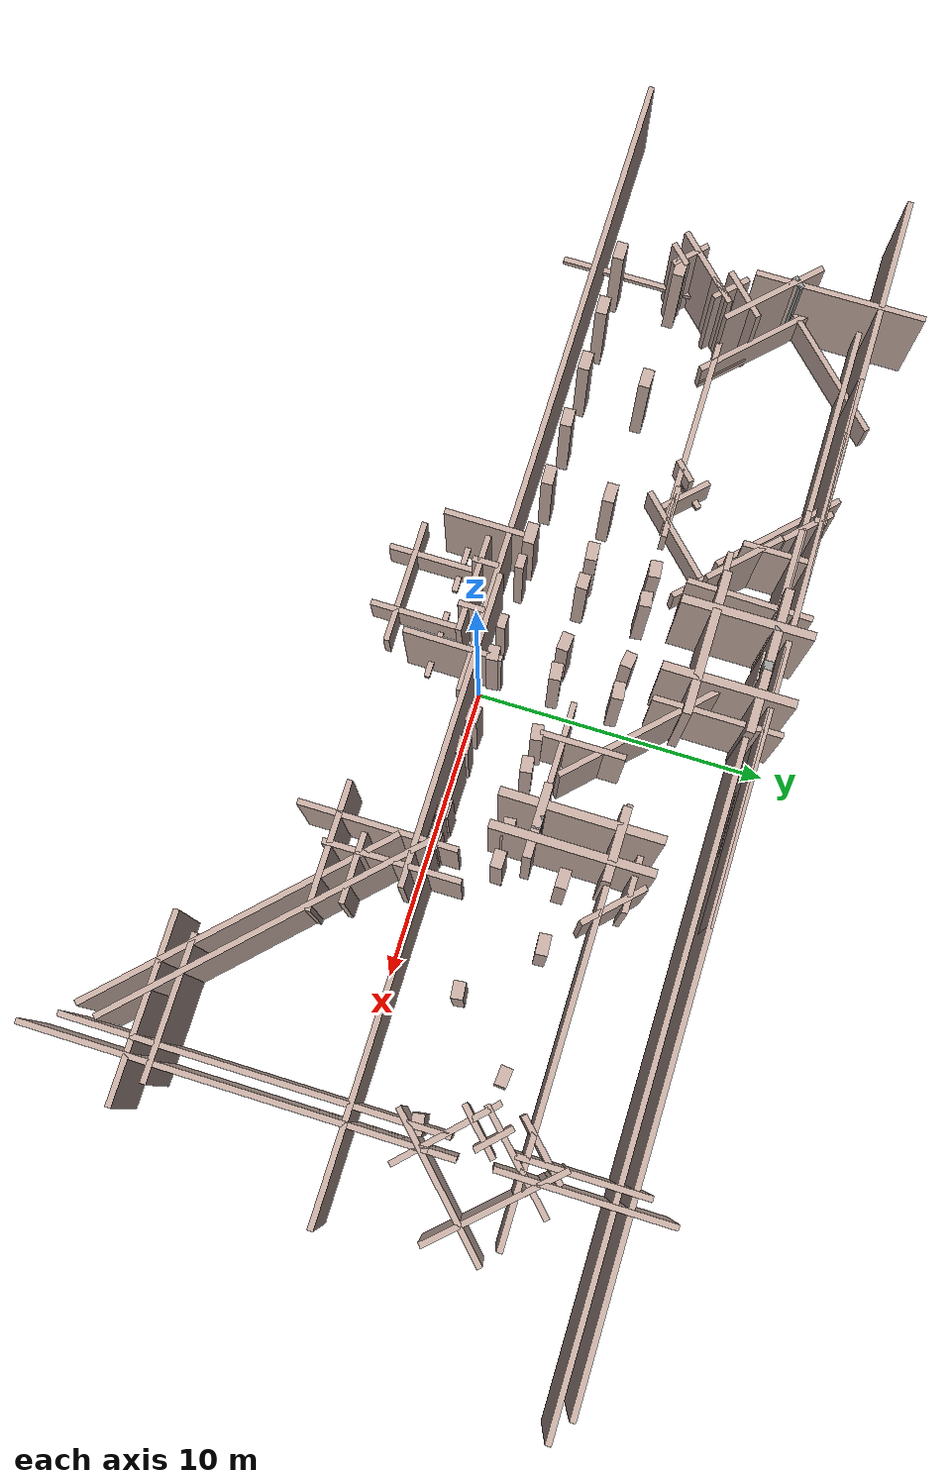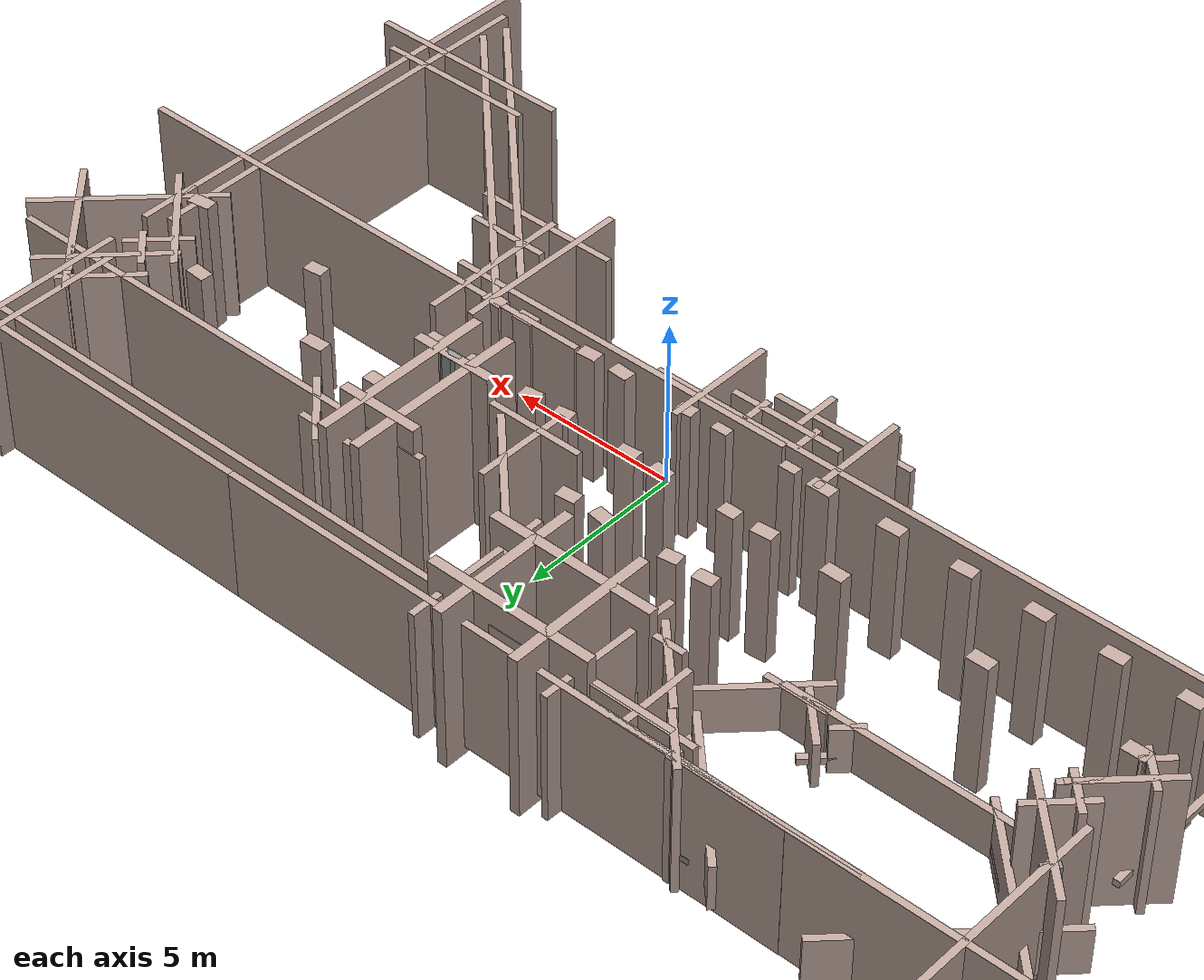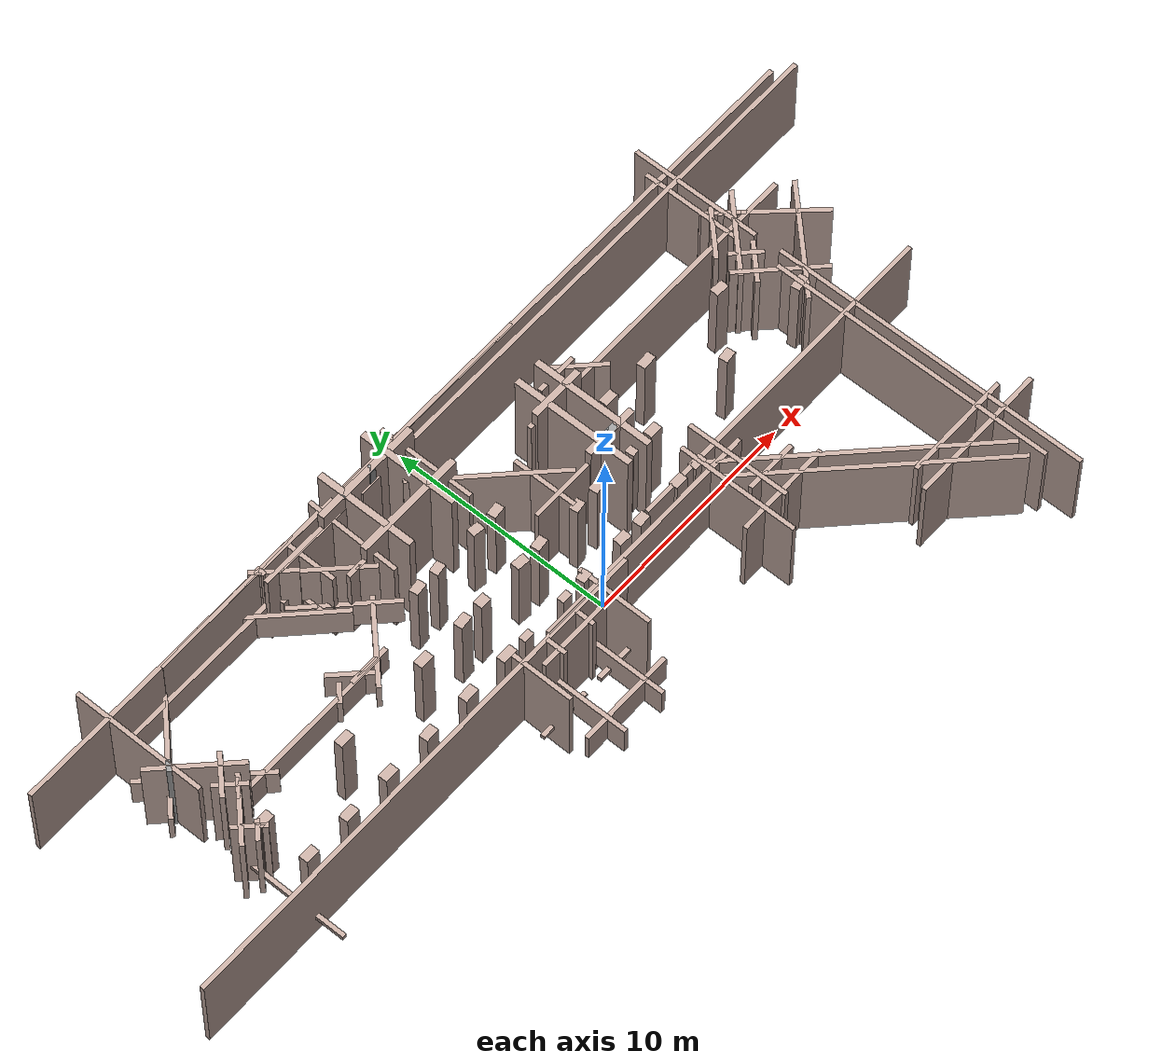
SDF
<?xml version='1.0' encoding='utf-8'?>
<sdf version="1.6">
  <model name="gedung_p">
    <pose frame="">0.050512 1.27019 0 0 -0 0</pose>
    <link name="Wall_104">
      <collision name="Wall_104_Collision">
        <geometry>
          <box>
            <size>2.89974 0.2 4.0</size>
          </box>
        </geometry>
        <pose frame="">0 0 1 0 -0 0</pose>
      </collision>
      <visual name="Wall_104_Visual">
        <pose frame="">0 0 1 0 -0 0</pose>
        <geometry>
          <box>
            <size>2.89974 0.2 4.0</size>
          </box>
        </geometry>
        <material>
          <script>
            <uri>file://media/materials/scripts/gazebo.material</uri>
            <name>Gazebo/Grey</name>
          </script>
          <ambient>0.760784 0.662745 0.627451 1</ambient>
        </material>
        <meta>
          <layer>0</layer>
        </meta>
      </visual>
      <pose frame="">-6.41651 6.00131 0 0 -0 -0.785922</pose>
    </link>
    <link name="Wall_105">
      <collision name="Wall_105_Collision">
        <geometry>
          <box>
            <size>1.9 0.2 4.0</size>
          </box>
        </geometry>
        <pose frame="">0 0 1 0 -0 0</pose>
      </collision>
      <visual name="Wall_105_Visual">
        <pose frame="">0 0 1 0 -0 0</pose>
        <geometry>
          <box>
            <size>1.9 0.2 4.0</size>
          </box>
        </geometry>
        <material>
          <script>
            <uri>file://media/materials/scripts/gazebo.material</uri>
            <name>Gazebo/Grey</name>
          </script>
          <ambient>0.760784 0.662745 0.627451 1</ambient>
        </material>
        <meta>
          <layer>0</layer>
        </meta>
      </visual>
      <pose frame="">-5.51451 5.52381 0 0 -0 0</pose>
    </link>
    <link name="Wall_108">
      <collision name="Wall_108_Collision">
        <geometry>
          <box>
            <size>5.0 0.3 5.0</size>
          </box>
        </geometry>
        <pose frame="">0 0 1.25 0 -0 0</pose>
      </collision>
      <visual name="Wall_108_Visual">
        <pose frame="">0 0 1.25 0 -0 0</pose>
        <geometry>
          <box>
            <size>5.0 0.3 5.0</size>
          </box>
        </geometry>
        <material>
          <script>
            <uri>file://media/materials/scripts/gazebo.material</uri>
            <name>Gazebo/Grey</name>
          </script>
          <ambient>0.760784 0.662745 0.627451 1</ambient>
        </material>
        <meta>
          <layer>0</layer>
        </meta>
      </visual>
      <pose frame="">-3.04751 7.6698 0 0 -0 0</pose>
    </link>
    <link name="Wall_11">
      <collision name="Wall_11_Collision">
        <geometry>
          <box>
            <size>3.0 0.2 4.0</size>
          </box>
        </geometry>
        <pose frame="">0 0 1 0 -0 0</pose>
      </collision>
      <visual name="Wall_11_Visual">
        <pose frame="">0 0 1 0 -0 0</pose>
        <geometry>
          <box>
            <size>3.0 0.2 4.0</size>
          </box>
        </geometry>
        <material>
          <script>
            <uri>file://media/materials/scripts/gazebo.material</uri>
            <name>Gazebo/Grey</name>
          </script>
          <ambient>0.760784 0.662745 0.627451 1</ambient>
        </material>
        <meta>
          <layer>0</layer>
        </meta>
      </visual>
      <pose frame="">-16.1925 2.05681 0 0 -0 0.785398</pose>
    </link>
    <link name="Wall_116">
      <collision name="Wall_116_Collision">
        <geometry>
          <box>
            <size>2.40092 0.2 0.2</size>
          </box>
        </geometry>
        <pose frame="">0 0 0.05 0 -0 0</pose>
      </collision>
      <visual name="Wall_116_Visual">
        <pose frame="">0 0 0.05 0 -0 0</pose>
        <geometry>
          <box>
            <size>2.40092 0.2 0.2</size>
          </box>
        </geometry>
        <material>
          <script>
            <uri>file://media/materials/scripts/gazebo.material</uri>
            <name>Gazebo/Grey</name>
          </script>
          <ambient>1 1 1 1</ambient>
        </material>
        <meta>
          <layer>0</layer>
        </meta>
      </visual>
      <pose frame="">-7.82151 8.1548 0 0 -0 3.14159</pose>
    </link>
    <link name="Wall_119">
      <collision name="Wall_119_Collision">
        <geometry>
          <box>
            <size>17.4 0.2 4.0</size>
          </box>
        </geometry>
        <pose frame="">0 0 1 0 -0 0</pose>
      </collision>
      <visual name="Wall_119_Visual">
        <pose frame="">0 0 1 0 -0 0</pose>
        <geometry>
          <box>
            <size>17.4 0.2 4.0</size>
          </box>
        </geometry>
        <material>
          <script>
            <uri>file://media/materials/scripts/gazebo.material</uri>
            <name>Gazebo/Grey</name>
          </script>
          <ambient>0.760784 0.662745 0.627451 1</ambient>
        </material>
        <meta>
          <layer>0</layer>
        </meta>
      </visual>
      <pose frame="">-2.97151 8.1548 0 0 -0 0</pose>
    </link>
    <link name="Wall_122">
      <collision name="Wall_122_Collision">
        <geometry>
          <box>
            <size>4.9 0.2 1.4</size>
          </box>
        </geometry>
        <pose frame="">0 0 0.35 0 -0 0</pose>
      </collision>
      <visual name="Wall_122_Visual">
        <pose frame="">0 0 0.35 0 -0 0</pose>
        <geometry>
          <box>
            <size>4.9 0.2 1.4</size>
          </box>
        </geometry>
        <material>
          <script>
            <uri>file://media/materials/scripts/gazebo.material</uri>
            <name>Gazebo/Grey</name>
          </script>
          <ambient>0.760784 0.662745 0.627451 1</ambient>
        </material>
        <meta>
          <layer>0</layer>
        </meta>
      </visual>
      <pose frame="">-8.34851 6.9748 0 0 -0 -0.785398</pose>
    </link>
    <link name="Wall_124">
      <collision name="Wall_124_Collision">
        <geometry>
          <box>
            <size>2.4 0.2 4.0</size>
          </box>
        </geometry>
        <pose frame="">0 0 1 0 -0 0</pose>
      </collision>
      <visual name="Wall_124_Visual">
        <pose frame="">0 0 1 0 -0 0</pose>
        <geometry>
          <box>
            <size>2.4 0.2 4.0</size>
          </box>
        </geometry>
        <material>
          <script>
            <uri>file://media/materials/scripts/gazebo.material</uri>
            <name>Gazebo/Grey</name>
          </script>
          <ambient>0.760784 0.662745 0.627451 1</ambient>
        </material>
        <meta>
          <layer>0</layer>
        </meta>
      </visual>
      <pose frame="">-6.89351 7.02881 0 0 -0 1.5708</pose>
    </link>
    <link name="Wall_125">
      <collision name="Wall_125_Collision">
        <geometry>
          <box>
            <size>3.9 0.2 4.0</size>
          </box>
        </geometry>
        <pose frame="">0 0 1 0 -0 0</pose>
      </collision>
      <visual name="Wall_125_Visual">
        <pose frame="">0 0 1 0 -0 0</pose>
        <geometry>
          <box>
            <size>3.9 0.2 4.0</size>
          </box>
        </geometry>
        <material>
          <script>
            <uri>file://media/materials/scripts/gazebo.material</uri>
            <name>Gazebo/Grey</name>
          </script>
          <ambient>0.760784 0.662745 0.627451 1</ambient>
        </material>
        <meta>
          <layer>0</layer>
        </meta>
      </visual>
      <pose frame="">-5.96851 7.57881 0 0 -0 0</pose>
    </link>
    <link name="Wall_126">
      <collision name="Wall_126_Collision">
        <geometry>
          <box>
            <size>4.31102 0.2 4.0</size>
          </box>
        </geometry>
        <pose frame="">0 0 1 0 -0 0</pose>
      </collision>
      <visual name="Wall_126_Visual">
        <pose frame="">0 0 1 0 -0 0</pose>
        <geometry>
          <box>
            <size>4.31102 0.2 4.0</size>
          </box>
        </geometry>
        <material>
          <script>
            <uri>file://media/materials/scripts/gazebo.material</uri>
            <name>Gazebo/Grey</name>
          </script>
          <ambient>0.760784 0.662745 0.627451 1</ambient>
        </material>
        <meta>
          <layer>0</layer>
        </meta>
      </visual>
      <pose frame="">-5.06651 6.55131 0 0 -0 -1.59318</pose>
    </link>
    <link name="Wall_128">
      <collision name="Wall_128_Collision">
        <geometry>
          <box>
            <size>4.5 0.3 5.0</size>
          </box>
        </geometry>
        <pose frame="">0 0 1.25 0 -0 0</pose>
      </collision>
      <visual name="Wall_128_Visual">
        <pose frame="">0 0 1.25 0 -0 0</pose>
        <geometry>
          <box>
            <size>4.5 0.3 5.0</size>
          </box>
        </geometry>
        <material>
          <script>
            <uri>file://media/materials/scripts/gazebo.material</uri>
            <name>Gazebo/Grey</name>
          </script>
          <ambient>0.760784 0.662745 0.627451 1</ambient>
        </material>
        <meta>
          <layer>0</layer>
        </meta>
      </visual>
      <pose frame="">-4.22251 6.61981 0 0 -0 -1.5708</pose>
    </link>
    <link name="Wall_129">
      <collision name="Wall_129_Collision">
        <geometry>
          <box>
            <size>5.0 0.3 5.0</size>
          </box>
        </geometry>
        <pose frame="">0 0 1.25 0 -0 0</pose>
      </collision>
      <visual name="Wall_129_Visual">
        <pose frame="">0 0 1.25 0 -0 0</pose>
        <geometry>
          <box>
            <size>5.0 0.3 5.0</size>
          </box>
        </geometry>
        <material>
          <script>
            <uri>file://media/materials/scripts/gazebo.material</uri>
            <name>Gazebo/Grey</name>
          </script>
          <ambient>0.760784 0.662745 0.627451 1</ambient>
        </material>
        <meta>
          <layer>0</layer>
        </meta>
      </visual>
      <pose frame="">-3.04751 5.5698 0 0 -0 0</pose>
    </link>
    <link name="Wall_130">
      <collision name="Wall_130_Collision">
        <geometry>
          <box>
            <size>4.5 0.3 5.0</size>
          </box>
        </geometry>
        <pose frame="">0 0 1.25 0 -0 0</pose>
      </collision>
      <visual name="Wall_130_Visual">
        <pose frame="">0 0 1.25 0 -0 0</pose>
        <geometry>
          <box>
            <size>4.5 0.3 5.0</size>
          </box>
        </geometry>
        <material>
          <script>
            <uri>file://media/materials/scripts/gazebo.material</uri>
            <name>Gazebo/Grey</name>
          </script>
          <ambient>0.760784 0.662745 0.627451 1</ambient>
        </material>
        <meta>
          <layer>0</layer>
        </meta>
      </visual>
      <pose frame="">-1.87251 6.61981 0 0 -0 1.5708</pose>
    </link>
    <link name="Wall_132">
      <collision name="Wall_132_Collision">
        <geometry>
          <box>
            <size>4.40008 0.2 4.0</size>
          </box>
        </geometry>
        <pose frame="">0 0 1 0 -0 0</pose>
      </collision>
      <visual name="Wall_132_Visual">
        <pose frame="">0 0 1 0 -0 0</pose>
        <geometry>
          <box>
            <size>4.40008 0.2 4.0</size>
          </box>
        </geometry>
        <material>
          <script>
            <uri>file://media/materials/scripts/gazebo.material</uri>
            <name>Gazebo/Grey</name>
          </script>
          <ambient>0.760784 0.662745 0.627451 1</ambient>
        </material>
        <meta>
          <layer>0</layer>
        </meta>
      </visual>
      <pose frame="">-0.943512 6.5908 0 0 -0 -1.5708</pose>
    </link>
    <link name="Wall_137">
      <collision name="Wall_137_Collision">
        <geometry>
          <box>
            <size>6.40062 0.2 4.0</size>
          </box>
        </geometry>
        <pose frame="">0 0 1 0 -0 0</pose>
      </collision>
      <visual name="Wall_137_Visual">
        <pose frame="">0 0 1 0 -0 0</pose>
        <geometry>
          <box>
            <size>6.40062 0.2 4.0</size>
          </box>
        </geometry>
        <material>
          <script>
            <uri>file://media/materials/scripts/gazebo.material</uri>
            <name>Gazebo/Grey</name>
          </script>
          <ambient>0.760784 0.662745 0.627451 1</ambient>
        </material>
        <meta>
          <layer>0</layer>
        </meta>
      </visual>
      <pose frame="">0.152488 4.4448 0 0 -0 -0.785398</pose>
    </link>
    <link name="Wall_138">
      <collision name="Wall_138_Collision">
        <geometry>
          <box>
            <size>2.90014 0.2 4.0</size>
          </box>
        </geometry>
        <pose frame="">0 0 1 0 -0 0</pose>
      </collision>
      <visual name="Wall_138_Visual">
        <pose frame="">0 0 1 0 -0 0</pose>
        <geometry>
          <box>
            <size>2.90014 0.2 4.0</size>
          </box>
        </geometry>
        <material>
          <script>
            <uri>file://media/materials/scripts/gazebo.material</uri>
            <name>Gazebo/Grey</name>
          </script>
          <ambient>0.760784 0.662745 0.627451 1</ambient>
        </material>
        <meta>
          <layer>0</layer>
        </meta>
      </visual>
      <pose frame="">1.24849 2.67381 0 0 -0 -1.5708</pose>
    </link>
    <link name="Wall_139">
      <collision name="Wall_139_Collision">
        <geometry>
          <box>
            <size>4.90086 0.2 4.0</size>
          </box>
        </geometry>
        <pose frame="">0 0 1 0 -0 0</pose>
      </collision>
      <visual name="Wall_139_Visual">
        <pose frame="">0 0 1 0 -0 0</pose>
        <geometry>
          <box>
            <size>4.90086 0.2 4.0</size>
          </box>
        </geometry>
        <material>
          <script>
            <uri>file://media/materials/scripts/gazebo.material</uri>
            <name>Gazebo/Grey</name>
          </script>
          <ambient>0.760784 0.662745 0.627451 1</ambient>
        </material>
        <meta>
          <layer>0</layer>
        </meta>
      </visual>
      <pose frame="">2.42349 1.9988 0 0 -0 0</pose>
    </link>
    <link name="Wall_140">
      <collision name="Wall_140_Collision">
        <geometry>
          <box>
            <size>5.5 0.3 5.0</size>
          </box>
        </geometry>
        <pose frame="">0 0 1.25 0 -0 0</pose>
      </collision>
      <visual name="Wall_140_Visual">
        <pose frame="">0 0 1.25 0 -0 0</pose>
        <geometry>
          <box>
            <size>5.5 0.3 5.0</size>
          </box>
        </geometry>
        <material>
          <script>
            <uri>file://media/materials/scripts/gazebo.material</uri>
            <name>Gazebo/Grey</name>
          </script>
          <ambient>0.760784 0.662745 0.627451 1</ambient>
        </material>
        <meta>
          <layer>0</layer>
        </meta>
      </visual>
      <pose frame="">3.59849 3.29881 0 0 -0 1.5708</pose>
    </link>
    <link name="Wall_141">
      <collision name="Wall_141_Collision">
        <geometry>
          <box>
            <size>2.5 0.3 5.0</size>
          </box>
        </geometry>
        <pose frame="">0 0 1.25 0 -0 0</pose>
      </collision>
      <visual name="Wall_141_Visual">
        <pose frame="">0 0 1.25 0 -0 0</pose>
        <geometry>
          <box>
            <size>2.5 0.3 5.0</size>
          </box>
        </geometry>
        <material>
          <script>
            <uri>file://media/materials/scripts/gazebo.material</uri>
            <name>Gazebo/Grey</name>
          </script>
          <ambient>0.760784 0.662745 0.627451 1</ambient>
        </material>
        <meta>
          <layer>0</layer>
        </meta>
      </visual>
      <pose frame="">4.14849 4.5988 0 0 -0 0</pose>
    </link>
    <link name="Wall_142">
      <collision name="Wall_142_Collision">
        <geometry>
          <box>
            <size>5.5 0.3 5.0</size>
          </box>
        </geometry>
        <pose frame="">0 0 1.25 0 -0 0</pose>
      </collision>
      <visual name="Wall_142_Visual">
        <pose frame="">0 0 1.25 0 -0 0</pose>
        <geometry>
          <box>
            <size>5.5 0.3 5.0</size>
          </box>
        </geometry>
        <material>
          <script>
            <uri>file://media/materials/scripts/gazebo.material</uri>
            <name>Gazebo/Grey</name>
          </script>
          <ambient>0.760784 0.662745 0.627451 1</ambient>
        </material>
        <meta>
          <layer>0</layer>
        </meta>
      </visual>
      <pose frame="">4.69849 3.29881 0 0 -0 -1.5708</pose>
    </link>
    <link name="Wall_143">
      <collision name="Wall_143_Collision">
        <geometry>
          <box>
            <size>2.5 0.3 5.0</size>
          </box>
        </geometry>
        <pose frame="">0 0 1.25 0 -0 0</pose>
      </collision>
      <visual name="Wall_143_Visual">
        <pose frame="">0 0 1.25 0 -0 0</pose>
        <geometry>
          <box>
            <size>2.5 0.3 5.0</size>
          </box>
        </geometry>
        <material>
          <script>
            <uri>file://media/materials/scripts/gazebo.material</uri>
            <name>Gazebo/Grey</name>
          </script>
          <ambient>0.760784 0.662745 0.627451 1</ambient>
        </material>
        <meta>
          <layer>0</layer>
        </meta>
      </visual>
      <pose frame="">4.14849 1.9988 0 0 -0 3.14159</pose>
    </link>
    <link name="Wall_145">
      <collision name="Wall_145_Collision">
        <geometry>
          <box>
            <size>30.5 0.2 4.0</size>
          </box>
        </geometry>
        <pose frame="">0 0 1 0 -0 0</pose>
      </collision>
      <visual name="Wall_145_Visual">
        <pose frame="">0 0 1 0 -0 0</pose>
        <geometry>
          <box>
            <size>30.5 0.2 4.0</size>
          </box>
        </geometry>
        <material>
          <script>
            <uri>file://media/materials/scripts/gazebo.material</uri>
            <name>Gazebo/Grey</name>
          </script>
          <ambient>0.760784 0.662745 0.627451 1</ambient>
        </material>
        <meta>
          <layer>0</layer>
        </meta>
      </visual>
      <pose frame="">6.63149 7.64081 0 0 -0 0</pose>
    </link>
    <link name="Wall_147">
      <collision name="Wall_147_Collision">
        <geometry>
          <box>
            <size>2.4 0.2 0.2</size>
          </box>
        </geometry>
        <pose frame="">0 0 0.05 0 -0 0</pose>
      </collision>
      <visual name="Wall_147_Visual">
        <pose frame="">0 0 0.05 0 -0 0</pose>
        <geometry>
          <box>
            <size>2.4 0.2 0.2</size>
          </box>
        </geometry>
        <material>
          <script>
            <uri>file://media/materials/scripts/gazebo.material</uri>
            <name>Gazebo/Grey</name>
          </script>
          <ambient>0.760784 0.662745 0.627451 1</ambient>
        </material>
        <meta>
          <layer>0</layer>
        </meta>
      </visual>
      <pose frame="">1.87849 8.1548 0 0 -0 0</pose>
    </link>
    <link name="Wall_149">
      <collision name="Wall_149_Collision">
        <geometry>
          <box>
            <size>1.9 0.2 4.0</size>
          </box>
        </geometry>
        <pose frame="">0 0 1 0 -0 0</pose>
      </collision>
      <visual name="Wall_149_Visual">
        <pose frame="">0 0 1 0 -0 0</pose>
        <geometry>
          <box>
            <size>1.9 0.2 4.0</size>
          </box>
        </geometry>
        <material>
          <script>
            <uri>file://media/materials/scripts/gazebo.material</uri>
            <name>Gazebo/Grey</name>
          </script>
          <ambient>0.760784 0.662745 0.627451 1</ambient>
        </material>
        <meta>
          <layer>0</layer>
        </meta>
      </visual>
      <pose frame="">4.69849 5.02381 0 0 -0 1.5708</pose>
    </link>
    <link name="Wall_150">
      <collision name="Wall_150_Collision">
        <geometry>
          <box>
            <size>1.9 0.2 4.0</size>
          </box>
        </geometry>
        <pose frame="">0 0 1 0 -0 0</pose>
      </collision>
      <visual name="Wall_150_Visual">
        <pose frame="">0 0 1 0 -0 0</pose>
        <geometry>
          <box>
            <size>1.9 0.2 4.0</size>
          </box>
        </geometry>
        <material>
          <script>
            <uri>file://media/materials/scripts/gazebo.material</uri>
            <name>Gazebo/Grey</name>
          </script>
          <ambient>0.760784 0.662745 0.627451 1</ambient>
        </material>
        <meta>
          <layer>0</layer>
        </meta>
      </visual>
      <pose frame="">5.12349 5.44881 0 0 -0 0</pose>
    </link>
    <link name="Wall_151">
      <collision name="Wall_151_Collision">
        <geometry>
          <box>
            <size>2.4 0.2 4.0</size>
          </box>
        </geometry>
        <pose frame="">0 0 1 0 -0 0</pose>
      </collision>
      <visual name="Wall_151_Visual">
        <pose frame="">0 0 1 0 -0 0</pose>
        <geometry>
          <box>
            <size>2.4 0.2 4.0</size>
          </box>
        </geometry>
        <material>
          <script>
            <uri>file://media/materials/scripts/gazebo.material</uri>
            <name>Gazebo/Grey</name>
          </script>
          <ambient>0.760784 0.662745 0.627451 1</ambient>
        </material>
        <meta>
          <layer>0</layer>
        </meta>
      </visual>
      <pose frame="">5.93749 5.0598 0 0 -0 -0.785398</pose>
    </link>
    <link name="Wall_152">
      <collision name="Wall_152_Collision">
        <geometry>
          <box>
            <size>14.4 0.2 4.0</size>
          </box>
        </geometry>
        <pose frame="">0 0 1 0 -0 0</pose>
      </collision>
      <visual name="Wall_152_Visual">
        <pose frame="">0 0 1 0 -0 0</pose>
        <geometry>
          <box>
            <size>14.4 0.2 4.0</size>
          </box>
        </geometry>
        <material>
          <script>
            <uri>file://media/materials/scripts/gazebo.material</uri>
            <name>Gazebo/Grey</name>
          </script>
          <ambient>0.760784 0.662745 0.627451 1</ambient>
        </material>
        <meta>
          <layer>0</layer>
        </meta>
      </visual>
      <pose frame="">9.87649 4.6708 0 0 -0 0</pose>
    </link>
    <link name="Wall_154">
      <collision name="Wall_154_Collision">
        <geometry>
          <box>
            <size>2.40052 0.2 4.0</size>
          </box>
        </geometry>
        <pose frame="">0 0 1 0 -0 0</pose>
      </collision>
      <visual name="Wall_154_Visual">
        <pose frame="">0 0 1 0 -0 0</pose>
        <geometry>
          <box>
            <size>2.40052 0.2 4.0</size>
          </box>
        </geometry>
        <material>
          <script>
            <uri>file://media/materials/scripts/gazebo.material</uri>
            <name>Gazebo/Grey</name>
          </script>
          <ambient>0.760784 0.662745 0.627451 1</ambient>
        </material>
        <meta>
          <layer>0</layer>
        </meta>
      </visual>
      <pose frame="">13.8155 5.0598 0 0 -0 0.785398</pose>
    </link>
    <link name="Wall_155">
      <collision name="Wall_155_Collision">
        <geometry>
          <box>
            <size>4.39964 0.2 4.0</size>
          </box>
        </geometry>
        <pose frame="">0 0 1 0 -0 0</pose>
      </collision>
      <visual name="Wall_155_Visual">
        <pose frame="">0 0 1 0 -0 0</pose>
        <geometry>
          <box>
            <size>4.39964 0.2 4.0</size>
          </box>
        </geometry>
        <material>
          <script>
            <uri>file://media/materials/scripts/gazebo.material</uri>
            <name>Gazebo/Grey</name>
          </script>
          <ambient>0.760784 0.662745 0.627451 1</ambient>
        </material>
        <meta>
          <layer>0</layer>
        </meta>
      </visual>
      <pose frame="">14.2045 6.4988 0 0 -0 1.5708</pose>
    </link>
    <link name="Wall_157">
      <collision name="Wall_157_Collision">
        <geometry>
          <box>
            <size>24.9 0.2 4.0</size>
          </box>
        </geometry>
        <pose frame="">0 0 1 0 -0 0</pose>
      </collision>
      <visual name="Wall_157_Visual">
        <pose frame="">0 0 1 0 -0 0</pose>
        <geometry>
          <box>
            <size>24.9 0.2 4.0</size>
          </box>
        </geometry>
        <material>
          <script>
            <uri>file://media/materials/scripts/gazebo.material</uri>
            <name>Gazebo/Grey</name>
          </script>
          <ambient>0.760784 0.662745 0.627451 1</ambient>
        </material>
        <meta>
          <layer>0</layer>
        </meta>
      </visual>
      <pose frame="">8.60349 8.1548 0 0 -0 0</pose>
    </link>
    <link name="Wall_159">
      <collision name="Wall_159_Collision">
        <geometry>
          <box>
            <size>5.9 0.2 4.0</size>
          </box>
        </geometry>
        <pose frame="">0 0 1 0 -0 0</pose>
      </collision>
      <visual name="Wall_159_Visual">
        <pose frame="">0 0 1 0 -0 0</pose>
        <geometry>
          <box>
            <size>5.9 0.2 4.0</size>
          </box>
        </geometry>
        <material>
          <script>
            <uri>file://media/materials/scripts/gazebo.material</uri>
            <name>Gazebo/Grey</name>
          </script>
          <ambient>0.760784 0.662745 0.627451 1</ambient>
        </material>
        <meta>
          <layer>0</layer>
        </meta>
      </visual>
      <pose frame="">14.7785 6.7298 0 0 -0 -1.5708</pose>
    </link>
    <link name="Wall_161">
      <collision name="Wall_161_Collision">
        <geometry>
          <box>
            <size>0.898622 0.2 4.0</size>
          </box>
        </geometry>
        <pose frame="">0 0 1 0 -0 0</pose>
      </collision>
      <visual name="Wall_161_Visual">
        <pose frame="">0 0 1 0 -0 0</pose>
        <geometry>
          <box>
            <size>0.898622 0.2 4.0</size>
          </box>
        </geometry>
        <material>
          <script>
            <uri>file://media/materials/scripts/gazebo.material</uri>
            <name>Gazebo/Grey</name>
          </script>
          <ambient>0.760784 0.662745 0.627451 1</ambient>
        </material>
        <meta>
          <layer>0</layer>
        </meta>
      </visual>
      <pose frame="">14.902 5.18131 0 0 -0 -0.785398</pose>
    </link>
    <link name="Wall_162">
      <collision name="Wall_162_Collision">
        <geometry>
          <box>
            <size>3.9 0.2 4.0</size>
          </box>
        </geometry>
        <pose frame="">0 0 1 0 -0 0</pose>
      </collision>
      <visual name="Wall_162_Visual">
        <pose frame="">0 0 1 0 -0 0</pose>
        <geometry>
          <box>
            <size>3.9 0.2 4.0</size>
          </box>
        </geometry>
        <material>
          <script>
            <uri>file://media/materials/scripts/gazebo.material</uri>
            <name>Gazebo/Grey</name>
          </script>
          <ambient>0.760784 0.662745 0.627451 1</ambient>
        </material>
        <meta>
          <layer>0</layer>
        </meta>
      </visual>
      <pose frame="">14.3715 4.4033 0 0 -0 -2.35581</pose>
    </link>
    <link name="Wall_164">
      <collision name="Wall_164_Collision">
        <geometry>
          <box>
            <size>1.399964 0.2 4.0</size>
          </box>
        </geometry>
        <pose frame="">0 0 1 0 -0 0</pose>
      </collision>
      <visual name="Wall_164_Visual">
        <pose frame="">0 0 1 0 -0 0</pose>
        <geometry>
          <box>
            <size>1.399964 0.2 4.0</size>
          </box>
        </geometry>
        <material>
          <script>
            <uri>file://media/materials/scripts/gazebo.material</uri>
            <name>Gazebo/Grey</name>
          </script>
          <ambient>0.760784 0.662745 0.627451 1</ambient>
        </material>
        <meta>
          <layer>0</layer>
        </meta>
      </visual>
      <pose frame="">13.93 3.53681 0 0 -0 -0.78422</pose>
    </link>
    <link name="Wall_165">
      <collision name="Wall_165_Collision">
        <geometry>
          <box>
            <size>1.900418 0.2 4.0</size>
          </box>
        </geometry>
        <pose frame="">0 0 1 0 -0 0</pose>
      </collision>
      <visual name="Wall_165_Visual">
        <pose frame="">0 0 1 0 -0 0</pose>
        <geometry>
          <box>
            <size>1.900418 0.2 4.0</size>
          </box>
        </geometry>
        <material>
          <script>
            <uri>file://media/materials/scripts/gazebo.material</uri>
            <name>Gazebo/Grey</name>
          </script>
          <ambient>0.760784 0.662745 0.627451 1</ambient>
        </material>
        <meta>
          <layer>0</layer>
        </meta>
      </visual>
      <pose frame="">13.842 3.02431 0 0 -0 -2.35619</pose>
    </link>
    <link name="Wall_166">
      <collision name="Wall_166_Collision">
        <geometry>
          <box>
            <size>3.8993 0.2 4.0</size>
          </box>
        </geometry>
        <pose frame="">0 0 1 0 -0 0</pose>
      </collision>
      <visual name="Wall_166_Visual">
        <pose frame="">0 0 1 0 -0 0</pose>
        <geometry>
          <box>
            <size>3.8993 0.2 4.0</size>
          </box>
        </geometry>
        <material>
          <script>
            <uri>file://media/materials/scripts/gazebo.material</uri>
            <name>Gazebo/Grey</name>
          </script>
          <ambient>0.760784 0.662745 0.627451 1</ambient>
        </material>
        <meta>
          <layer>0</layer>
        </meta>
      </visual>
      <pose frame="">14.1955 2.06981 0 0 -0 -0.785398</pose>
    </link>
    <link name="Wall_169">
      <collision name="Wall_169_Collision">
        <geometry>
          <box>
            <size>5.39864 0.2 4.0</size>
          </box>
        </geometry>
        <pose frame="">0 0 1 0 -0 0</pose>
      </collision>
      <visual name="Wall_169_Visual">
        <pose frame="">0 0 1 0 -0 0</pose>
        <geometry>
          <box>
            <size>5.39864 0.2 4.0</size>
          </box>
        </geometry>
        <material>
          <script>
            <uri>file://media/materials/scripts/gazebo.material</uri>
            <name>Gazebo/Grey</name>
          </script>
          <ambient>0.760784 0.662745 0.627451 1</ambient>
        </material>
        <meta>
          <layer>0</layer>
        </meta>
      </visual>
      <pose frame="">15.7685 2.3348 0 0 -0 0.785398</pose>
    </link>
    <link name="Wall_17">
      <collision name="Wall_17_Collision">
        <geometry>
          <box>
            <size>0.899858 0.2 4.0</size>
          </box>
        </geometry>
        <pose frame="">0 0 1 0 -0 0</pose>
      </collision>
      <visual name="Wall_17_Visual">
        <pose frame="">0 0 1 0 -0 0</pose>
        <geometry>
          <box>
            <size>0.899858 0.2 4.0</size>
          </box>
        </geometry>
        <material>
          <script>
            <uri>file://media/materials/scripts/gazebo.material</uri>
            <name>Gazebo/Grey</name>
          </script>
          <ambient>0.760784 0.662745 0.627451 1</ambient>
        </material>
        <meta>
          <layer>0</layer>
        </meta>
      </visual>
      <pose frame="">-15.574 2.6753 0 0 -0 0.785398</pose>
    </link>
    <link name="Wall_173">
      <collision name="Wall_173_Collision">
        <geometry>
          <box>
            <size>5.10546 0.2 4.0</size>
          </box>
        </geometry>
        <pose frame="">0 0 1 0 -0 0</pose>
      </collision>
      <visual name="Wall_173_Visual">
        <pose frame="">0 0 1 0 -0 0</pose>
        <geometry>
          <box>
            <size>5.10546 0.2 4.0</size>
          </box>
        </geometry>
        <material>
          <script>
            <uri>file://media/materials/scripts/gazebo.material</uri>
            <name>Gazebo/Grey</name>
          </script>
          <ambient>0.760784 0.662745 0.627451 1</ambient>
        </material>
        <meta>
          <layer>0</layer>
        </meta>
      </visual>
      <pose frame="">15.8565 4.1558 0 0 -0 -0.826345</pose>
    </link>
    <link name="Wall_175">
      <collision name="Wall_175_Collision">
        <geometry>
          <box>
            <size>0.9 0.2 4.0</size>
          </box>
        </geometry>
        <pose frame="">0 0 1 0 -0 0</pose>
      </collision>
      <visual name="Wall_175_Visual">
        <pose frame="">0 0 1 0 -0 0</pose>
        <geometry>
          <box>
            <size>0.9 0.2 4.0</size>
          </box>
        </geometry>
        <material>
          <script>
            <uri>file://media/materials/scripts/gazebo.material</uri>
            <name>Gazebo/Grey</name>
          </script>
          <ambient>0.760784 0.662745 0.627451 1</ambient>
        </material>
        <meta>
          <layer>0</layer>
        </meta>
      </visual>
      <pose frame="">14.8495 1.2408 0 0 -0 -1.5708</pose>
    </link>
    <link name="Wall_176">
      <collision name="Wall_176_Collision">
        <geometry>
          <box>
            <size>4.4 0.2 0.2</size>
          </box>
        </geometry>
        <pose frame="">0 0 0.05 0 -0 0</pose>
      </collision>
      <visual name="Wall_176_Visual">
        <pose frame="">0 0 0.05 0 -0 0</pose>
        <geometry>
          <box>
            <size>4.4 0.2 0.2</size>
          </box>
        </geometry>
        <material>
          <script>
            <uri>file://media/materials/scripts/gazebo.material</uri>
            <name>Gazebo/Grey</name>
          </script>
          <ambient>0.760784 0.662745 0.627451 1</ambient>
        </material>
        <meta>
          <layer>0</layer>
        </meta>
      </visual>
      <pose frame="">14.8495 0.015805 0 0 -0 -1.5708</pose>
    </link>
    <link name="Wall_178">
      <collision name="Wall_178_Collision">
        <geometry>
          <box>
            <size>14.4 0.2 4.0</size>
          </box>
        </geometry>
        <pose frame="">0 0 1 0 -0 0</pose>
      </collision>
      <visual name="Wall_178_Visual">
        <pose frame="">0 0 1 0 -0 0</pose>
        <geometry>
          <box>
            <size>14.4 0.2 4.0</size>
          </box>
        </geometry>
        <material>
          <script>
            <uri>file://media/materials/scripts/gazebo.material</uri>
            <name>Gazebo/Grey</name>
          </script>
          <ambient>0.760784 0.662745 0.627451 1</ambient>
        </material>
        <meta>
          <layer>0</layer>
        </meta>
      </visual>
      <pose frame="">14.8495 -4.5842 0 0 -0 -1.5708</pose>
    </link>
    <link name="Wall_18">
      <collision name="Wall_18_Collision">
        <geometry>
          <box>
            <size>1.4 0.2 4.0</size>
          </box>
        </geometry>
        <pose frame="">0 0 1 0 -0 0</pose>
      </collision>
      <visual name="Wall_18_Visual">
        <pose frame="">0 0 1 0 -0 0</pose>
        <geometry>
          <box>
            <size>1.4 0.2 4.0</size>
          </box>
        </geometry>
        <material>
          <script>
            <uri>file://media/materials/scripts/gazebo.material</uri>
            <name>Gazebo/Grey</name>
          </script>
          <ambient>0.760784 0.662745 0.627451 1</ambient>
        </material>
        <meta>
          <layer>0</layer>
        </meta>
      </visual>
      <pose frame="">-15.6625 3.01131 0 0 -0 2.35502</pose>
    </link>
    <link name="Wall_180">
      <collision name="Wall_180_Collision">
        <geometry>
          <box>
            <size>6.4 0.2 4.0</size>
          </box>
        </geometry>
        <pose frame="">0 0 1 0 -0 0</pose>
      </collision>
      <visual name="Wall_180_Visual">
        <pose frame="">0 0 1 0 -0 0</pose>
        <geometry>
          <box>
            <size>6.4 0.2 4.0</size>
          </box>
        </geometry>
        <material>
          <script>
            <uri>file://media/materials/scripts/gazebo.material</uri>
            <name>Gazebo/Grey</name>
          </script>
          <ambient>0.760784 0.662745 0.627451 1</ambient>
        </material>
        <meta>
          <layer>0</layer>
        </meta>
      </visual>
      <pose frame="">13.2995 -8.1342 0 0 -0 3.14159</pose>
    </link>
    <link name="Wall_181">
      <collision name="Wall_181_Collision">
        <geometry>
          <box>
            <size>11.4 0.2 4.0</size>
          </box>
        </geometry>
        <pose frame="">0 0 1 0 -0 0</pose>
      </collision>
      <visual name="Wall_181_Visual">
        <pose frame="">0 0 1 0 -0 0</pose>
        <geometry>
          <box>
            <size>11.4 0.2 4.0</size>
          </box>
        </geometry>
        <material>
          <script>
            <uri>file://media/materials/scripts/gazebo.material</uri>
            <name>Gazebo/Grey</name>
          </script>
          <ambient>0.760784 0.662745 0.627451 1</ambient>
        </material>
        <meta>
          <layer>0</layer>
        </meta>
      </visual>
      <pose frame="">9.76949 -6.15419 0 0 -0 2.35619</pose>
    </link>
    <link name="Wall_182">
      <collision name="Wall_182_Collision">
        <geometry>
          <box>
            <size>4.4 0.2 4.0</size>
          </box>
        </geometry>
        <pose frame="">0 0 1 0 -0 0</pose>
      </collision>
      <visual name="Wall_182_Visual">
        <pose frame="">0 0 1 0 -0 0</pose>
        <geometry>
          <box>
            <size>4.4 0.2 4.0</size>
          </box>
        </geometry>
        <material>
          <script>
            <uri>file://media/materials/scripts/gazebo.material</uri>
            <name>Gazebo/Grey</name>
          </script>
          <ambient>0.760784 0.662745 0.627451 1</ambient>
        </material>
        <meta>
          <layer>0</layer>
        </meta>
      </visual>
      <pose frame="">6.73949 -4.1742 0 0 -0 3.14159</pose>
    </link>
    <link name="Wall_189">
      <collision name="Wall_189_Collision">
        <geometry>
          <box>
            <size>5.4 0.2 4.0</size>
          </box>
        </geometry>
        <pose frame="">0 0 1 0 -0 0</pose>
      </collision>
      <visual name="Wall_189_Visual">
        <pose frame="">0 0 1 0 -0 0</pose>
        <geometry>
          <box>
            <size>5.4 0.2 4.0</size>
          </box>
        </geometry>
        <material>
          <script>
            <uri>file://media/materials/scripts/gazebo.material</uri>
            <name>Gazebo/Grey</name>
          </script>
          <ambient>0.760784 0.662745 0.627451 1</ambient>
        </material>
        <meta>
          <layer>0</layer>
        </meta>
      </visual>
      <pose frame="">5.68949 -2.87419 0 0 -0 1.5708</pose>
    </link>
    <link name="Wall_19">
      <collision name="Wall_19_Collision">
        <geometry>
          <box>
            <size>1.899822 0.2 4.0</size>
          </box>
        </geometry>
        <pose frame="">0 0 1 0 -0 0</pose>
      </collision>
      <visual name="Wall_19_Visual">
        <pose frame="">0 0 1 0 -0 0</pose>
        <geometry>
          <box>
            <size>1.899822 0.2 4.0</size>
          </box>
        </geometry>
        <material>
          <script>
            <uri>file://media/materials/scripts/gazebo.material</uri>
            <name>Gazebo/Grey</name>
          </script>
          <ambient>0.760784 0.662745 0.627451 1</ambient>
        </material>
        <meta>
          <layer>0</layer>
        </meta>
      </visual>
      <pose frame="">-15.574 3.52431 0 0 -0 0.785398</pose>
    </link>
    <link name="Wall_190">
      <collision name="Wall_190_Collision">
        <geometry>
          <box>
            <size>2.378 0.2 0.2</size>
          </box>
        </geometry>
        <pose frame="">0 0 0.05 0 -0 0</pose>
      </collision>
      <visual name="Wall_190_Visual">
        <pose frame="">0 0 0.05 0 -0 0</pose>
        <geometry>
          <box>
            <size>2.378 0.2 0.2</size>
          </box>
        </geometry>
        <material>
          <script>
            <uri>file://media/materials/scripts/gazebo.material</uri>
            <name>Gazebo/Grey</name>
          </script>
          <ambient>0.760784 0.662745 0.627451 1</ambient>
        </material>
        <meta>
          <layer>0</layer>
        </meta>
      </visual>
      <pose frame="">5.14499 -1.5742 0 0 -0 3.14159</pose>
    </link>
    <link name="Wall_191">
      <collision name="Wall_191_Collision">
        <geometry>
          <box>
            <size>10.8997 0.2 4.0</size>
          </box>
        </geometry>
        <pose frame="">0 0 1 0 -0 0</pose>
      </collision>
      <visual name="Wall_191_Visual">
        <pose frame="">0 0 1 0 -0 0</pose>
        <geometry>
          <box>
            <size>10.8997 0.2 4.0</size>
          </box>
        </geometry>
        <material>
          <script>
            <uri>file://media/materials/scripts/gazebo.material</uri>
            <name>Gazebo/Grey</name>
          </script>
          <ambient>0.760784 0.662745 0.627451 1</ambient>
        </material>
        <meta>
          <layer>0</layer>
        </meta>
      </visual>
      <pose frame="">1.92549 -1.5742 0 0 -0 3.14159</pose>
    </link>
    <link name="Wall_192">
      <collision name="Wall_192_Collision">
        <geometry>
          <box>
            <size>3.40008 0.2 4.0</size>
          </box>
        </geometry>
        <pose frame="">0 0 1 0 -0 0</pose>
      </collision>
      <visual name="Wall_192_Visual">
        <pose frame="">0 0 1 0 -0 0</pose>
        <geometry>
          <box>
            <size>3.40008 0.2 4.0</size>
          </box>
        </geometry>
        <material>
          <script>
            <uri>file://media/materials/scripts/gazebo.material</uri>
            <name>Gazebo/Grey</name>
          </script>
          <ambient>0.760784 0.662745 0.627451 1</ambient>
        </material>
        <meta>
          <layer>0</layer>
        </meta>
      </visual>
      <pose frame="">-0.755012 -2.37419 0 0 -0 -1.57767</pose>
    </link>
    <link name="Wall_194">
      <collision name="Wall_194_Collision">
        <geometry>
          <box>
            <size>2.4 0.2 0.2</size>
          </box>
        </geometry>
        <pose frame="">0 0 0.05 0 -0 0</pose>
      </collision>
      <visual name="Wall_194_Visual">
        <pose frame="">0 0 0.05 0 -0 0</pose>
        <geometry>
          <box>
            <size>2.4 0.2 0.2</size>
          </box>
        </geometry>
        <material>
          <script>
            <uri>file://media/materials/scripts/gazebo.material</uri>
            <name>Gazebo/Grey</name>
          </script>
          <ambient>0.760784 0.662745 0.627451 1</ambient>
        </material>
        <meta>
          <layer>0</layer>
        </meta>
      </visual>
      <pose frame="">-1.31051 -3.1742 0 0 -0 3.14159</pose>
    </link>
    <link name="Wall_195">
      <collision name="Wall_195_Collision">
        <geometry>
          <box>
            <size>3.4 0.2 1.4</size>
          </box>
        </geometry>
        <pose frame="">0 0 0.35 0 -0 0</pose>
      </collision>
      <visual name="Wall_195_Visual">
        <pose frame="">0 0 0.35 0 -0 0</pose>
        <geometry>
          <box>
            <size>3.4 0.2 1.4</size>
          </box>
        </geometry>
        <material>
          <script>
            <uri>file://media/materials/scripts/gazebo.material</uri>
            <name>Gazebo/Grey</name>
          </script>
          <ambient>0.760784 0.662745 0.627451 1</ambient>
        </material>
        <meta>
          <layer>0</layer>
        </meta>
      </visual>
      <pose frame="">-1.86051 -3.97419 0 0 -0 -1.5708</pose>
    </link>
    <link name="Wall_196">
      <collision name="Wall_196_Collision">
        <geometry>
          <box>
            <size>4.4 0.2 1.4</size>
          </box>
        </geometry>
        <pose frame="">0 0 0.35 0 -0 0</pose>
      </collision>
      <visual name="Wall_196_Visual">
        <pose frame="">0 0 0.35 0 -0 0</pose>
        <geometry>
          <box>
            <size>4.4 0.2 1.4</size>
          </box>
        </geometry>
        <material>
          <script>
            <uri>file://media/materials/scripts/gazebo.material</uri>
            <name>Gazebo/Grey</name>
          </script>
          <ambient>0.760784 0.662745 0.627451 1</ambient>
        </material>
        <meta>
          <layer>0</layer>
        </meta>
      </visual>
      <pose frame="">-2.91051 -4.77419 0 0 -0 3.14159</pose>
    </link>
    <link name="Wall_197">
      <collision name="Wall_197_Collision">
        <geometry>
          <box>
            <size>3.4 0.2 1.4</size>
          </box>
        </geometry>
        <pose frame="">0 0 0.35 0 -0 0</pose>
      </collision>
      <visual name="Wall_197_Visual">
        <pose frame="">0 0 0.35 0 -0 0</pose>
        <geometry>
          <box>
            <size>3.4 0.2 1.4</size>
          </box>
        </geometry>
        <material>
          <script>
            <uri>file://media/materials/scripts/gazebo.material</uri>
            <name>Gazebo/Grey</name>
          </script>
          <ambient>0.760784 0.662745 0.627451 1</ambient>
        </material>
        <meta>
          <layer>0</layer>
        </meta>
      </visual>
      <pose frame="">-3.96051 -3.97419 0 0 -0 1.5708</pose>
    </link>
    <link name="Wall_198">
      <collision name="Wall_198_Collision">
        <geometry>
          <box>
            <size>2.4 0.2 0.2</size>
          </box>
        </geometry>
        <pose frame="">0 0 0.05 0 -0 0</pose>
      </collision>
      <visual name="Wall_198_Visual">
        <pose frame="">0 0 0.05 0 -0 0</pose>
        <geometry>
          <box>
            <size>2.4 0.2 0.2</size>
          </box>
        </geometry>
        <material>
          <script>
            <uri>file://media/materials/scripts/gazebo.material</uri>
            <name>Gazebo/Grey</name>
          </script>
          <ambient>0.760784 0.662745 0.627451 1</ambient>
        </material>
        <meta>
          <layer>0</layer>
        </meta>
      </visual>
      <pose frame="">-4.51051 -3.1742 0 0 -0 3.14159</pose>
    </link>
    <link name="Wall_199">
      <collision name="Wall_199_Collision">
        <geometry>
          <box>
            <size>3.10826 0.2 4.0</size>
          </box>
        </geometry>
        <pose frame="">0 0 1 0 -0 0</pose>
      </collision>
      <visual name="Wall_199_Visual">
        <pose frame="">0 0 1 0 -0 0</pose>
        <geometry>
          <box>
            <size>3.10826 0.2 4.0</size>
          </box>
        </geometry>
        <material>
          <script>
            <uri>file://media/materials/scripts/gazebo.material</uri>
            <name>Gazebo/Grey</name>
          </script>
          <ambient>0.760784 0.662745 0.627451 1</ambient>
        </material>
        <meta>
          <layer>0</layer>
        </meta>
      </visual>
      <pose frame="">-5.05601 -2.44719 0 0 -0 1.56461</pose>
    </link>
    <link name="Wall_201">
      <collision name="Wall_201_Collision">
        <geometry>
          <box>
            <size>0.9 0.2 4.0</size>
          </box>
        </geometry>
        <pose frame="">0 0 1 0 -0 0</pose>
      </collision>
      <visual name="Wall_201_Visual">
        <pose frame="">0 0 1 0 -0 0</pose>
        <geometry>
          <box>
            <size>0.9 0.2 4.0</size>
          </box>
        </geometry>
        <material>
          <script>
            <uri>file://media/materials/scripts/gazebo.material</uri>
            <name>Gazebo/Grey</name>
          </script>
          <ambient>0.760784 0.662745 0.627451 1</ambient>
        </material>
        <meta>
          <layer>0</layer>
        </meta>
      </visual>
      <pose frame="">-3.75851 -2.16319 0 0 -0 -1.5708</pose>
    </link>
    <link name="Wall_202">
      <collision name="Wall_202_Collision">
        <geometry>
          <box>
            <size>3.4 0.2 4.0</size>
          </box>
        </geometry>
        <pose frame="">0 0 1 0 -0 0</pose>
      </collision>
      <visual name="Wall_202_Visual">
        <pose frame="">0 0 1 0 -0 0</pose>
        <geometry>
          <box>
            <size>3.4 0.2 4.0</size>
          </box>
        </geometry>
        <material>
          <script>
            <uri>file://media/materials/scripts/gazebo.material</uri>
            <name>Gazebo/Grey</name>
          </script>
          <ambient>0.760784 0.662745 0.627451 1</ambient>
        </material>
        <meta>
          <layer>0</layer>
        </meta>
      </visual>
      <pose frame="">-2.95851 -2.33819 0 0 -0 0</pose>
    </link>
    <link name="Wall_203">
      <collision name="Wall_203_Collision">
        <geometry>
          <box>
            <size>0.900952 0.2 4.0</size>
          </box>
        </geometry>
        <pose frame="">0 0 1 0 -0 0</pose>
      </collision>
      <visual name="Wall_203_Visual">
        <pose frame="">0 0 1 0 -0 0</pose>
        <geometry>
          <box>
            <size>0.900952 0.2 4.0</size>
          </box>
        </geometry>
        <material>
          <script>
            <uri>file://media/materials/scripts/gazebo.material</uri>
            <name>Gazebo/Grey</name>
          </script>
          <ambient>0.760784 0.662745 0.627451 1</ambient>
        </material>
        <meta>
          <layer>0</layer>
        </meta>
      </visual>
      <pose frame="">-2.15851 -2.16319 0 0 -0 1.5708</pose>
    </link>
    <link name="Wall_205">
      <collision name="Wall_205_Collision">
        <geometry>
          <box>
            <size>15.4006 0.2 4.0</size>
          </box>
        </geometry>
        <pose frame="">0 0 1 0 -0 0</pose>
      </collision>
      <visual name="Wall_205_Visual">
        <pose frame="">0 0 1 0 -0 0</pose>
        <geometry>
          <box>
            <size>15.4006 0.2 4.0</size>
          </box>
        </geometry>
        <material>
          <script>
            <uri>file://media/materials/scripts/gazebo.material</uri>
            <name>Gazebo/Grey</name>
          </script>
          <ambient>0.760784 0.662745 0.627451 1</ambient>
        </material>
        <meta>
          <layer>0</layer>
        </meta>
      </visual>
      <pose frame="">10.4455 -0.995195 0 0 -0 -0.002895</pose>
    </link>
    <link name="Wall_206">
      <collision name="Wall_206_Collision">
        <geometry>
          <box>
            <size>12.87816 0.2 4.0</size>
          </box>
        </geometry>
        <pose frame="">0 0 1 0 -0 0</pose>
      </collision>
      <visual name="Wall_206_Visual">
        <pose frame="">0 0 1 0 -0 0</pose>
        <geometry>
          <box>
            <size>12.87816 0.2 4.0</size>
          </box>
        </geometry>
        <material>
          <script>
            <uri>file://media/materials/scripts/gazebo.material</uri>
            <name>Gazebo/Grey</name>
          </script>
          <ambient>0.760784 0.662745 0.627451 1</ambient>
        </material>
        <meta>
          <layer>0</layer>
        </meta>
      </visual>
      <pose frame="">14.2455 -4.1757 0 0 -0 -1.5708</pose>
    </link>
    <link name="Wall_209">
      <collision name="Wall_209_Collision">
        <geometry>
          <box>
            <size>4.89946 0.2 4.0</size>
          </box>
        </geometry>
        <pose frame="">0 0 1 0 -0 0</pose>
      </collision>
      <visual name="Wall_209_Visual">
        <pose frame="">0 0 1 0 -0 0</pose>
        <geometry>
          <box>
            <size>4.89946 0.2 4.0</size>
          </box>
        </geometry>
        <material>
          <script>
            <uri>file://media/materials/scripts/gazebo.material</uri>
            <name>Gazebo/Grey</name>
          </script>
          <ambient>0.760784 0.662745 0.627451 1</ambient>
        </material>
        <meta>
          <layer>0</layer>
        </meta>
      </visual>
      <pose frame="">13.0705 -7.3452 0 0 -0 3.14159</pose>
    </link>
    <link name="Wall_21">
      <collision name="Wall_21_Collision">
        <geometry>
          <box>
            <size>3.9 0.2 4.0</size>
          </box>
        </geometry>
        <pose frame="">0 0 1 0 -0 0</pose>
      </collision>
      <visual name="Wall_21_Visual">
        <pose frame="">0 0 1 0 -0 0</pose>
        <geometry>
          <box>
            <size>3.9 0.2 4.0</size>
          </box>
        </geometry>
        <material>
          <script>
            <uri>file://media/materials/scripts/gazebo.material</uri>
            <name>Gazebo/Grey</name>
          </script>
          <ambient>0.760784 0.662745 0.627451 1</ambient>
        </material>
        <meta>
          <layer>0</layer>
        </meta>
      </visual>
      <pose frame="">-15.9275 4.47881 0 0 -0 2.35619</pose>
    </link>
    <link name="Wall_210">
      <collision name="Wall_210_Collision">
        <geometry>
          <box>
            <size>11.8995 0.2 4.0</size>
          </box>
        </geometry>
        <pose frame="">0 0 1 0 -0 0</pose>
      </collision>
      <visual name="Wall_210_Visual">
        <pose frame="">0 0 1 0 -0 0</pose>
        <geometry>
          <box>
            <size>11.8995 0.2 4.0</size>
          </box>
        </geometry>
        <material>
          <script>
            <uri>file://media/materials/scripts/gazebo.material</uri>
            <name>Gazebo/Grey</name>
          </script>
          <ambient>0.760784 0.662745 0.627451 1</ambient>
        </material>
        <meta>
          <layer>0</layer>
        </meta>
      </visual>
      <pose frame="">9.82749 -5.27719 0 0 -0 2.35619</pose>
    </link>
    <link name="Wall_211">
      <collision name="Wall_211_Collision">
        <geometry>
          <box>
            <size>2.4 0.2 4.0</size>
          </box>
        </geometry>
        <pose frame="">0 0 1 0 -0 0</pose>
      </collision>
      <visual name="Wall_211_Visual">
        <pose frame="">0 0 1 0 -0 0</pose>
        <geometry>
          <box>
            <size>2.4 0.2 4.0</size>
          </box>
        </geometry>
        <material>
          <script>
            <uri>file://media/materials/scripts/gazebo.material</uri>
            <name>Gazebo/Grey</name>
          </script>
          <ambient>0.760784 0.662745 0.627451 1</ambient>
        </material>
        <meta>
          <layer>0</layer>
        </meta>
      </visual>
      <pose frame="">7.20949 -3.20919 0 0 -0 3.14159</pose>
    </link>
    <link name="Wall_214">
      <collision name="Wall_214_Collision">
        <geometry>
          <box>
            <size>4.64908 0.2 4.0</size>
          </box>
        </geometry>
        <pose frame="">0 0 1 0 -0 0</pose>
      </collision>
      <visual name="Wall_214_Visual">
        <pose frame="">0 0 1 0 -0 0</pose>
        <geometry>
          <box>
            <size>4.64908 0.2 4.0</size>
          </box>
        </geometry>
        <material>
          <script>
            <uri>file://media/materials/scripts/gazebo.material</uri>
            <name>Gazebo/Grey</name>
          </script>
          <ambient>0.760784 0.662745 0.627451 1</ambient>
        </material>
        <meta>
          <layer>0</layer>
        </meta>
      </visual>
      <pose frame="">6.65249 -2.09669 0 0 -0 -1.5645</pose>
    </link>
    <link name="Wall_218">
      <collision name="Wall_218_Collision">
        <geometry>
          <box>
            <size>0.644524 0.4 4.0</size>
          </box>
        </geometry>
        <pose frame="">0 0 1 0 -0 0</pose>
      </collision>
      <visual name="Wall_218_Visual">
        <pose frame="">0 0 1 0 -0 0</pose>
        <geometry>
          <box>
            <size>0.644524 0.4 4.0</size>
          </box>
        </geometry>
        <material>
          <script>
            <uri>file://media/materials/scripts/gazebo.material</uri>
            <name>Gazebo/Grey</name>
          </script>
          <ambient>0.760784 0.662745 0.627451 1</ambient>
        </material>
        <meta>
          <layer>0</layer>
        </meta>
      </visual>
      <pose frame="">-15.9022 -1.01464 0 0 -0 0</pose>
    </link>
    <link name="Wall_22">
      <collision name="Wall_22_Collision">
        <geometry>
          <box>
            <size>0.493318 0.2 4.0</size>
          </box>
        </geometry>
        <pose frame="">0 0 1 0 -0 0</pose>
      </collision>
      <visual name="Wall_22_Visual">
        <pose frame="">0 0 1 0 -0 0</pose>
        <geometry>
          <box>
            <size>0.493318 0.2 4.0</size>
          </box>
        </geometry>
        <material>
          <script>
            <uri>file://media/materials/scripts/gazebo.material</uri>
            <name>Gazebo/Grey</name>
          </script>
          <ambient>1 1 1 1</ambient>
        </material>
        <meta>
          <layer>0</layer>
        </meta>
      </visual>
      <pose frame="">-16.533 5.1878 0 0 -0 0.848118</pose>
    </link>
    <link name="Wall_220">
      <collision name="Wall_220_Collision">
        <geometry>
          <box>
            <size>0.66193 0.4 4.0</size>
          </box>
        </geometry>
        <pose frame="">0 0 1 0 -0 0</pose>
      </collision>
      <visual name="Wall_220_Visual">
        <pose frame="">0 0 1 0 -0 0</pose>
        <geometry>
          <box>
            <size>0.66193 0.4 4.0</size>
          </box>
        </geometry>
        <material>
          <script>
            <uri>file://media/materials/scripts/gazebo.material</uri>
            <name>Gazebo/Grey</name>
          </script>
          <ambient>0.760784 0.662745 0.627451 1</ambient>
        </material>
        <meta>
          <layer>0</layer>
        </meta>
      </visual>
      <pose frame="">-13.7647 -1.01253 0 0 -0 0.032247</pose>
    </link>
    <link name="Wall_223">
      <collision name="Wall_223_Collision">
        <geometry>
          <box>
            <size>0.67166 0.4 4.0</size>
          </box>
        </geometry>
        <pose frame="">0 0 1 0 -0 0</pose>
      </collision>
      <visual name="Wall_223_Visual">
        <pose frame="">0 0 1 0 -0 0</pose>
        <geometry>
          <box>
            <size>0.67166 0.4 4.0</size>
          </box>
        </geometry>
        <material>
          <script>
            <uri>file://media/materials/scripts/gazebo.material</uri>
            <name>Gazebo/Grey</name>
          </script>
          <ambient>0.760784 0.662745 0.627451 1</ambient>
        </material>
        <meta>
          <layer>0</layer>
        </meta>
      </visual>
      <pose frame="">-15.9129 1.14369 0 0 -0 3.14159</pose>
    </link>
    <link name="Wall_225">
      <collision name="Wall_225_Collision">
        <geometry>
          <box>
            <size>0.673398 0.4 4.0</size>
          </box>
        </geometry>
        <pose frame="">0 0 1 0 -0 0</pose>
      </collision>
      <visual name="Wall_225_Visual">
        <pose frame="">0 0 1 0 -0 0</pose>
        <geometry>
          <box>
            <size>0.673398 0.4 4.0</size>
          </box>
        </geometry>
        <material>
          <script>
            <uri>file://media/materials/scripts/gazebo.material</uri>
            <name>Gazebo/Grey</name>
          </script>
          <ambient>0.760784 0.662745 0.627451 1</ambient>
        </material>
        <meta>
          <layer>0</layer>
        </meta>
      </visual>
      <pose frame="">-11.6269 -1.00331 0 0 -0 0</pose>
    </link>
    <link name="Wall_227">
      <collision name="Wall_227_Collision">
        <geometry>
          <box>
            <size>0.641584 0.4 4.0</size>
          </box>
        </geometry>
        <pose frame="">0 0 1 0 -0 0</pose>
      </collision>
      <visual name="Wall_227_Visual">
        <pose frame="">0 0 1 0 -0 0</pose>
        <geometry>
          <box>
            <size>0.641584 0.4 4.0</size>
          </box>
        </geometry>
        <material>
          <script>
            <uri>file://media/materials/scripts/gazebo.material</uri>
            <name>Gazebo/Grey</name>
          </script>
          <ambient>0.760784 0.662745 0.627451 1</ambient>
        </material>
        <meta>
          <layer>0</layer>
        </meta>
      </visual>
      <pose frame="">-9.46431 -1.01152 0 0 -0 0.045423</pose>
    </link>
    <link name="Wall_229">
      <collision name="Wall_229_Collision">
        <geometry>
          <box>
            <size>0.684544 0.4 4.0</size>
          </box>
        </geometry>
        <pose frame="">0 0 1 0 -0 0</pose>
      </collision>
      <visual name="Wall_229_Visual">
        <pose frame="">0 0 1 0 -0 0</pose>
        <geometry>
          <box>
            <size>0.684544 0.4 4.0</size>
          </box>
        </geometry>
        <material>
          <script>
            <uri>file://media/materials/scripts/gazebo.material</uri>
            <name>Gazebo/Grey</name>
          </script>
          <ambient>0.760784 0.662745 0.627451 1</ambient>
        </material>
        <meta>
          <layer>0</layer>
        </meta>
      </visual>
      <pose frame="">-7.30446 -1.02245 0 0 -0 -3.10315</pose>
    </link>
    <link name="Wall_23">
      <collision name="Wall_23_Collision">
        <geometry>
          <box>
            <size>6.0 0.2 4.0</size>
          </box>
        </geometry>
        <pose frame="">0 0 1 0 -0 0</pose>
      </collision>
      <visual name="Wall_23_Visual">
        <pose frame="">0 0 1 0 -0 0</pose>
        <geometry>
          <box>
            <size>6.0 0.2 4.0</size>
          </box>
        </geometry>
        <material>
          <script>
            <uri>file://media/materials/scripts/gazebo.material</uri>
            <name>Gazebo/Grey</name>
          </script>
          <ambient>0.760784 0.662745 0.627451 1</ambient>
        </material>
        <meta>
          <layer>0</layer>
        </meta>
      </visual>
      <pose frame="">-16.4845 6.6928 0 0 -0 1.5708</pose>
    </link>
    <link name="Wall_231">
      <collision name="Wall_231_Collision">
        <geometry>
          <box>
            <size>0.717142 0.4 4.0</size>
          </box>
        </geometry>
        <pose frame="">0 0 1 0 -0 0</pose>
      </collision>
      <visual name="Wall_231_Visual">
        <pose frame="">0 0 1 0 -0 0</pose>
        <geometry>
          <box>
            <size>0.717142 0.4 4.0</size>
          </box>
        </geometry>
        <material>
          <script>
            <uri>file://media/materials/scripts/gazebo.material</uri>
            <name>Gazebo/Grey</name>
          </script>
          <ambient>0.760784 0.662745 0.627451 1</ambient>
        </material>
        <meta>
          <layer>0</layer>
        </meta>
      </visual>
      <pose frame="">-5.16375 -1.01425 0 0 -0 3.14159</pose>
    </link>
    <link name="Wall_233">
      <collision name="Wall_233_Collision">
        <geometry>
          <box>
            <size>0.520792 0.4 4.0</size>
          </box>
        </geometry>
        <pose frame="">0 0 1 0 -0 0</pose>
      </collision>
      <visual name="Wall_233_Visual">
        <pose frame="">0 0 1 0 -0 0</pose>
        <geometry>
          <box>
            <size>0.520792 0.4 4.0</size>
          </box>
        </geometry>
        <material>
          <script>
            <uri>file://media/materials/scripts/gazebo.material</uri>
            <name>Gazebo/Grey</name>
          </script>
          <ambient>0.760784 0.662745 0.627451 1</ambient>
        </material>
        <meta>
          <layer>0</layer>
        </meta>
      </visual>
      <pose frame="">-0.860454 -1.01152 0 0 -0 0.09066</pose>
    </link>
    <link name="Wall_235">
      <collision name="Wall_235_Collision">
        <geometry>
          <box>
            <size>0.59715 0.4 4.0</size>
          </box>
        </geometry>
        <pose frame="">0 0 1 0 -0 0</pose>
      </collision>
      <visual name="Wall_235_Visual">
        <pose frame="">0 0 1 0 -0 0</pose>
        <geometry>
          <box>
            <size>0.59715 0.4 4.0</size>
          </box>
        </geometry>
        <material>
          <script>
            <uri>file://media/materials/scripts/gazebo.material</uri>
            <name>Gazebo/Grey</name>
          </script>
          <ambient>0.760784 0.662745 0.627451 1</ambient>
        </material>
        <meta>
          <layer>0</layer>
        </meta>
      </visual>
      <pose frame="">1.29119 -1.02245 0 0 -0 -0.055499</pose>
    </link>
    <link name="Wall_237">
      <collision name="Wall_237_Collision">
        <geometry>
          <box>
            <size>0.585912 0.4 4.0</size>
          </box>
        </geometry>
        <pose frame="">0 0 1 0 -0 0</pose>
      </collision>
      <visual name="Wall_237_Visual">
        <pose frame="">0 0 1 0 -0 0</pose>
        <geometry>
          <box>
            <size>0.585912 0.4 4.0</size>
          </box>
        </geometry>
        <material>
          <script>
            <uri>file://media/materials/scripts/gazebo.material</uri>
            <name>Gazebo/Grey</name>
          </script>
          <ambient>0.760784 0.662745 0.627451 1</ambient>
        </material>
        <meta>
          <layer>0</layer>
        </meta>
      </visual>
      <pose frame="">2.36565 -1.02792 0 0 -0 -3.08284</pose>
    </link>
    <link name="Wall_239">
      <collision name="Wall_239_Collision">
        <geometry>
          <box>
            <size>0.61981 0.4 4.0</size>
          </box>
        </geometry>
        <pose frame="">0 0 1 0 -0 0</pose>
      </collision>
      <visual name="Wall_239_Visual">
        <pose frame="">0 0 1 0 -0 0</pose>
        <geometry>
          <box>
            <size>0.61981 0.4 4.0</size>
          </box>
        </geometry>
        <material>
          <script>
            <uri>file://media/materials/scripts/gazebo.material</uri>
            <name>Gazebo/Grey</name>
          </script>
          <ambient>0.760784 0.662745 0.627451 1</ambient>
        </material>
        <meta>
          <layer>0</layer>
        </meta>
      </visual>
      <pose frame="">4.51183 -1.00878 0 0 -0 0</pose>
    </link>
    <link name="Wall_242">
      <collision name="Wall_242_Collision">
        <geometry>
          <box>
            <size>0.3 0.3 5.0</size>
          </box>
        </geometry>
        <pose frame="">0 0 1.25 0 -0 0</pose>
      </collision>
      <visual name="Wall_242_Visual">
        <pose frame="">0 0 1.25 0 -0 0</pose>
        <geometry>
          <box>
            <size>0.3 0.3 5.0</size>
          </box>
        </geometry>
        <material>
          <script>
            <uri>file://media/materials/scripts/gazebo.material</uri>
            <name>Gazebo/Grey</name>
          </script>
          <ambient>1 1 1 1</ambient>
        </material>
        <meta>
          <layer>0</layer>
        </meta>
      </visual>
      <pose frame="">4.28764 2.00954 0 0 -0 0</pose>
    </link>
    <link name="Wall_244">
      <collision name="Wall_244_Collision">
        <geometry>
          <box>
            <size>0.5 0.3 5.0</size>
          </box>
        </geometry>
        <pose frame="">0 0 1.25 0 -0 0</pose>
      </collision>
      <visual name="Wall_244_Visual">
        <pose frame="">0 0 1.25 0 -0 0</pose>
        <geometry>
          <box>
            <size>0.5 0.3 5.0</size>
          </box>
        </geometry>
        <material>
          <script>
            <uri>file://media/materials/scripts/gazebo.material</uri>
            <name>Gazebo/Grey</name>
          </script>
          <ambient>1 1 1 1</ambient>
        </material>
        <meta>
          <layer>0</layer>
        </meta>
      </visual>
      <pose frame="">4.23218 2.00954 0 0 -0 3.14159</pose>
    </link>
    <link name="Wall_246">
      <collision name="Wall_246_Collision">
        <geometry>
          <box>
            <size>0.618992 0.4 4.0</size>
          </box>
        </geometry>
        <pose frame="">0 0 1 0 -0 0</pose>
      </collision>
      <visual name="Wall_246_Visual">
        <pose frame="">0 0 1 0 -0 0</pose>
        <geometry>
          <box>
            <size>0.618992 0.4 4.0</size>
          </box>
        </geometry>
        <material>
          <script>
            <uri>file://media/materials/scripts/gazebo.material</uri>
            <name>Gazebo/Grey</name>
          </script>
          <ambient>0.760784 0.662745 0.627451 1</ambient>
        </material>
        <meta>
          <layer>0</layer>
        </meta>
      </visual>
      <pose frame="">5.59996 -1.01699 0 0 -0 -0.049958</pose>
    </link>
    <link name="Wall_248">
      <collision name="Wall_248_Collision">
        <geometry>
          <box>
            <size>0.689444 0.4 4.0</size>
          </box>
        </geometry>
        <pose frame="">0 0 1 0 -0 0</pose>
      </collision>
      <visual name="Wall_248_Visual">
        <pose frame="">0 0 1 0 -0 0</pose>
        <geometry>
          <box>
            <size>0.689444 0.4 4.0</size>
          </box>
        </geometry>
        <material>
          <script>
            <uri>file://media/materials/scripts/gazebo.material</uri>
            <name>Gazebo/Grey</name>
          </script>
          <ambient>0.760784 0.662745 0.627451 1</ambient>
        </material>
        <meta>
          <layer>0</layer>
        </meta>
      </visual>
      <pose frame="">14.197 1.14518 0 0 -0 0.132552</pose>
    </link>
    <link name="Wall_25">
      <collision name="Wall_25_Collision">
        <geometry>
          <box>
            <size>16.4078 0.2 4.0</size>
          </box>
        </geometry>
        <pose frame="">0 0 1 0 -0 0</pose>
      </collision>
      <visual name="Wall_25_Visual">
        <pose frame="">0 0 1 0 -0 0</pose>
        <geometry>
          <box>
            <size>16.4078 0.2 4.0</size>
          </box>
        </geometry>
        <material>
          <script>
            <uri>file://media/materials/scripts/gazebo.material</uri>
            <name>Gazebo/Grey</name>
          </script>
          <ambient>0.760784 0.662745 0.627451 1</ambient>
        </material>
        <meta>
          <layer>0</layer>
        </meta>
      </visual>
      <pose frame="">-12.4325 8.1463 0 0 -0 0.000864</pose>
    </link>
    <link name="Wall_250">
      <collision name="Wall_250_Collision">
        <geometry>
          <box>
            <size>0.573202 0.4 4.0</size>
          </box>
        </geometry>
        <pose frame="">0 0 1 0 -0 0</pose>
      </collision>
      <visual name="Wall_250_Visual">
        <pose frame="">0 0 1 0 -0 0</pose>
        <geometry>
          <box>
            <size>0.573202 0.4 4.0</size>
          </box>
        </geometry>
        <material>
          <script>
            <uri>file://media/materials/scripts/gazebo.material</uri>
            <name>Gazebo/Grey</name>
          </script>
          <ambient>0.760784 0.662745 0.627451 1</ambient>
        </material>
        <meta>
          <layer>0</layer>
        </meta>
      </visual>
      <pose frame="">9.91253 1.1404 0 0 -0 0.110657</pose>
    </link>
    <link name="Wall_252">
      <collision name="Wall_252_Collision">
        <geometry>
          <box>
            <size>0.610398 0.4 4.0</size>
          </box>
        </geometry>
        <pose frame="">0 0 1 0 -0 0</pose>
      </collision>
      <visual name="Wall_252_Visual">
        <pose frame="">0 0 1 0 -0 0</pose>
        <geometry>
          <box>
            <size>0.610398 0.4 4.0</size>
          </box>
        </geometry>
        <material>
          <script>
            <uri>file://media/materials/scripts/gazebo.material</uri>
            <name>Gazebo/Grey</name>
          </script>
          <ambient>0.760784 0.662745 0.627451 1</ambient>
        </material>
        <meta>
          <layer>0</layer>
        </meta>
      </visual>
      <pose frame="">5.58982 1.13562 0 0 -0 0</pose>
    </link>
    <link name="Wall_254">
      <collision name="Wall_254_Collision">
        <geometry>
          <box>
            <size>0.649386 0.4 4.0</size>
          </box>
        </geometry>
        <pose frame="">0 0 1 0 -0 0</pose>
      </collision>
      <visual name="Wall_254_Visual">
        <pose frame="">0 0 1 0 -0 0</pose>
        <geometry>
          <box>
            <size>0.649386 0.4 4.0</size>
          </box>
        </geometry>
        <material>
          <script>
            <uri>file://media/materials/scripts/gazebo.material</uri>
            <name>Gazebo/Grey</name>
          </script>
          <ambient>0.760784 0.662745 0.627451 1</ambient>
        </material>
        <meta>
          <layer>0</layer>
        </meta>
      </visual>
      <pose frame="">5.58982 3.28741 0 0 -0 0</pose>
    </link>
    <link name="Wall_256">
      <collision name="Wall_256_Collision">
        <geometry>
          <box>
            <size>0.687542 0.4 4.0</size>
          </box>
        </geometry>
        <pose frame="">0 0 1 0 -0 0</pose>
      </collision>
      <visual name="Wall_256_Visual">
        <pose frame="">0 0 1 0 -0 0</pose>
        <geometry>
          <box>
            <size>0.687542 0.4 4.0</size>
          </box>
        </geometry>
        <material>
          <script>
            <uri>file://media/materials/scripts/gazebo.material</uri>
            <name>Gazebo/Grey</name>
          </script>
          <ambient>0.760784 0.662745 0.627451 1</ambient>
        </material>
        <meta>
          <layer>0</layer>
        </meta>
      </visual>
      <pose frame="">7.7703 3.28263 0 0 -0 0.066568</pose>
    </link>
    <link name="Wall_258">
      <collision name="Wall_258_Collision">
        <geometry>
          <box>
            <size>0.63032 0.4 4.0</size>
          </box>
        </geometry>
        <pose frame="">0 0 1 0 -0 0</pose>
      </collision>
      <visual name="Wall_258_Visual">
        <pose frame="">0 0 1 0 -0 0</pose>
        <geometry>
          <box>
            <size>0.63032 0.4 4.0</size>
          </box>
        </geometry>
        <material>
          <script>
            <uri>file://media/materials/scripts/gazebo.material</uri>
            <name>Gazebo/Grey</name>
          </script>
          <ambient>0.760784 0.662745 0.627451 1</ambient>
        </material>
        <meta>
          <layer>0</layer>
        </meta>
      </visual>
      <pose frame="">12.0309 3.27306 0 0 -0 -0.083141</pose>
    </link>
    <link name="Wall_26">
      <collision name="Wall_26_Collision">
        <geometry>
          <box>
            <size>7.1878 0.2 4.0</size>
          </box>
        </geometry>
        <pose frame="">0 0 1 0 -0 0</pose>
      </collision>
      <visual name="Wall_26_Visual">
        <pose frame="">0 0 1 0 -0 0</pose>
        <geometry>
          <box>
            <size>7.1878 0.2 4.0</size>
          </box>
        </geometry>
        <material>
          <script>
            <uri>file://media/materials/scripts/gazebo.material</uri>
            <name>Gazebo/Grey</name>
          </script>
          <ambient>0.760784 0.662745 0.627451 1</ambient>
        </material>
        <meta>
          <layer>0</layer>
        </meta>
      </visual>
      <pose frame="">-10.1275 8.1463 0 0 -0 -3.13959</pose>
    </link>
    <link name="Wall_260">
      <collision name="Wall_260_Collision">
        <geometry>
          <box>
            <size>0.63032 0.4 4.0</size>
          </box>
        </geometry>
        <pose frame="">0 0 1 0 -0 0</pose>
      </collision>
      <visual name="Wall_260_Visual">
        <pose frame="">0 0 1 0 -0 0</pose>
        <geometry>
          <box>
            <size>0.63032 0.4 4.0</size>
          </box>
        </geometry>
        <material>
          <script>
            <uri>file://media/materials/scripts/gazebo.material</uri>
            <name>Gazebo/Grey</name>
          </script>
          <ambient>0.760784 0.662745 0.627451 1</ambient>
        </material>
        <meta>
          <layer>0</layer>
        </meta>
      </visual>
      <pose frame="">4.52349 1.1404 0 0 -0 0.083141</pose>
    </link>
    <link name="Wall_262">
      <collision name="Wall_262_Collision">
        <geometry>
          <box>
            <size>0.535248 0.4 4.0</size>
          </box>
        </geometry>
        <pose frame="">0 0 1 0 -0 0</pose>
      </collision>
      <visual name="Wall_262_Visual">
        <pose frame="">0 0 1 0 -0 0</pose>
        <geometry>
          <box>
            <size>0.535248 0.4 4.0</size>
          </box>
        </geometry>
        <material>
          <script>
            <uri>file://media/materials/scripts/gazebo.material</uri>
            <name>Gazebo/Grey</name>
          </script>
          <ambient>0.760784 0.662745 0.627451 1</ambient>
        </material>
        <meta>
          <layer>0</layer>
        </meta>
      </visual>
      <pose frame="">1.27667 1.13083 0 0 -0 0.141897</pose>
    </link>
    <link name="Wall_264">
      <collision name="Wall_264_Collision">
        <geometry>
          <box>
            <size>0.554208 0.4 4.0</size>
          </box>
        </geometry>
        <pose frame="">0 0 1 0 -0 0</pose>
      </collision>
      <visual name="Wall_264_Visual">
        <pose frame="">0 0 1 0 -0 0</pose>
        <geometry>
          <box>
            <size>0.554208 0.4 4.0</size>
          </box>
        </geometry>
        <material>
          <script>
            <uri>file://media/materials/scripts/gazebo.material</uri>
            <name>Gazebo/Grey</name>
          </script>
          <ambient>0.760784 0.662745 0.627451 1</ambient>
        </material>
        <meta>
          <layer>0</layer>
        </meta>
      </visual>
      <pose frame="">2.38126 1.12127 0 0 -0 0.124355</pose>
    </link>
    <link name="Wall_266">
      <collision name="Wall_266_Collision">
        <geometry>
          <box>
            <size>0.66846 0.4 4.0</size>
          </box>
        </geometry>
        <pose frame="">0 0 1 0 -0 0</pose>
      </collision>
      <visual name="Wall_266_Visual">
        <pose frame="">0 0 1 0 -0 0</pose>
        <geometry>
          <box>
            <size>0.66846 0.4 4.0</size>
          </box>
        </geometry>
        <material>
          <script>
            <uri>file://media/materials/scripts/gazebo.material</uri>
            <name>Gazebo/Grey</name>
          </script>
          <ambient>0.760784 0.662745 0.627451 1</ambient>
        </material>
        <meta>
          <layer>0</layer>
        </meta>
      </visual>
      <pose frame="">-11.6102 1.14518 0 0 -0 0</pose>
    </link>
    <link name="Wall_268">
      <collision name="Wall_268_Collision">
        <geometry>
          <box>
            <size>0.667778 0.4 4.0</size>
          </box>
        </geometry>
        <pose frame="">0 0 1 0 -0 0</pose>
      </collision>
      <visual name="Wall_268_Visual">
        <pose frame="">0 0 1 0 -0 0</pose>
        <geometry>
          <box>
            <size>0.667778 0.4 4.0</size>
          </box>
        </geometry>
        <material>
          <script>
            <uri>file://media/materials/scripts/gazebo.material</uri>
            <name>Gazebo/Grey</name>
          </script>
          <ambient>0.760784 0.662745 0.627451 1</ambient>
        </material>
        <meta>
          <layer>0</layer>
        </meta>
      </visual>
      <pose frame="">-7.29702 1.12605 0 0 -0 3.14159</pose>
    </link>
    <link name="Wall_270">
      <collision name="Wall_270_Collision">
        <geometry>
          <box>
            <size>0.63032 0.4 4.0</size>
          </box>
        </geometry>
        <pose frame="">0 0 1 0 -0 0</pose>
      </collision>
      <visual name="Wall_270_Visual">
        <pose frame="">0 0 1 0 -0 0</pose>
        <geometry>
          <box>
            <size>0.63032 0.4 4.0</size>
          </box>
        </geometry>
        <material>
          <script>
            <uri>file://media/materials/scripts/gazebo.material</uri>
            <name>Gazebo/Grey</name>
          </script>
          <ambient>0.760784 0.662745 0.627451 1</ambient>
        </material>
        <meta>
          <layer>0</layer>
        </meta>
      </visual>
      <pose frame="">-5.1548 1.12127 0 0 -0 0.083141</pose>
    </link>
    <link name="Wall_272">
      <collision name="Wall_272_Collision">
        <geometry>
          <box>
            <size>0.53389 0.4 4.0</size>
          </box>
        </geometry>
        <pose frame="">0 0 1 0 -0 0</pose>
      </collision>
      <visual name="Wall_272_Visual">
        <pose frame="">0 0 1 0 -0 0</pose>
        <geometry>
          <box>
            <size>0.53389 0.4 4.0</size>
          </box>
        </geometry>
        <material>
          <script>
            <uri>file://media/materials/scripts/gazebo.material</uri>
            <name>Gazebo/Grey</name>
          </script>
          <ambient>0.760784 0.662745 0.627451 1</ambient>
        </material>
        <meta>
          <layer>0</layer>
        </meta>
      </visual>
      <pose frame="">-4.06934 1.12605 0 0 -0 0</pose>
    </link>
    <link name="Wall_274">
      <collision name="Wall_274_Collision">
        <geometry>
          <box>
            <size>0.573202 0.4 4.0</size>
          </box>
        </geometry>
        <pose frame="">0 0 1 0 -0 0</pose>
      </collision>
      <visual name="Wall_274_Visual">
        <pose frame="">0 0 1 0 -0 0</pose>
        <geometry>
          <box>
            <size>0.573202 0.4 4.0</size>
          </box>
        </geometry>
        <material>
          <script>
            <uri>file://media/materials/scripts/gazebo.material</uri>
            <name>Gazebo/Grey</name>
          </script>
          <ambient>0.760784 0.662745 0.627451 1</ambient>
        </material>
        <meta>
          <layer>0</layer>
        </meta>
      </visual>
      <pose frame="">-5.16914 3.28263 0 0 -0 0.110657</pose>
    </link>
    <link name="Wall_276">
      <collision name="Wall_276_Collision">
        <geometry>
          <box>
            <size>0.535248 0.4 4.0</size>
          </box>
        </geometry>
        <pose frame="">0 0 1 0 -0 0</pose>
      </collision>
      <visual name="Wall_276_Visual">
        <pose frame="">0 0 1 0 -0 0</pose>
        <geometry>
          <box>
            <size>0.535248 0.4 4.0</size>
          </box>
        </geometry>
        <material>
          <script>
            <uri>file://media/materials/scripts/gazebo.material</uri>
            <name>Gazebo/Grey</name>
          </script>
          <ambient>0.760784 0.662745 0.627451 1</ambient>
        </material>
        <meta>
          <layer>0</layer>
        </meta>
      </visual>
      <pose frame="">-4.08846 3.27306 0 0 -0 0.141897</pose>
    </link>
    <link name="Wall_278">
      <collision name="Wall_278_Collision">
        <geometry>
          <box>
            <size>1.0 0.4 4.0</size>
          </box>
        </geometry>
        <pose frame="">0 0 1 0 -0 0</pose>
      </collision>
      <visual name="Wall_278_Visual">
        <pose frame="">0 0 1 0 -0 0</pose>
        <geometry>
          <box>
            <size>1.0 0.4 4.0</size>
          </box>
        </geometry>
        <material>
          <script>
            <uri>file://media/materials/scripts/gazebo.material</uri>
            <name>Gazebo/Grey</name>
          </script>
          <ambient>0.760784 0.662745 0.627451 1</ambient>
        </material>
        <meta>
          <layer>0</layer>
        </meta>
      </visual>
      <pose frame="">-3.00554 7.6387 0 0 -0 0</pose>
    </link>
    <link name="Wall_279">
      <collision name="Wall_279_Collision">
        <geometry>
          <box>
            <size>0.3 0.3 5.0</size>
          </box>
        </geometry>
        <pose frame="">0 0 1.25 0 -0 0</pose>
      </collision>
      <visual name="Wall_279_Visual">
        <pose frame="">0 0 1.25 0 -0 0</pose>
        <geometry>
          <box>
            <size>0.3 0.3 5.0</size>
          </box>
        </geometry>
        <material>
          <script>
            <uri>file://media/materials/scripts/gazebo.material</uri>
            <name>Gazebo/Grey</name>
          </script>
          <ambient>1 1 1 1</ambient>
        </material>
        <meta>
          <layer>0</layer>
        </meta>
      </visual>
      <pose frame="">-2.85554 7.6387 0 0 -0 0</pose>
    </link>
    <link name="Wall_28">
      <collision name="Wall_28_Collision">
        <geometry>
          <box>
            <size>0.414774 0.2 4.0</size>
          </box>
        </geometry>
        <pose frame="">0 0 1 0 -0 0</pose>
      </collision>
      <visual name="Wall_28_Visual">
        <pose frame="">0 0 1 0 -0 0</pose>
        <geometry>
          <box>
            <size>0.414774 0.2 4.0</size>
          </box>
        </geometry>
        <material>
          <script>
            <uri>file://media/materials/scripts/gazebo.material</uri>
            <name>Gazebo/Grey</name>
          </script>
          <ambient>0.760784 0.662745 0.627451 1</ambient>
        </material>
        <meta>
          <layer>0</layer>
        </meta>
      </visual>
      <pose frame="">-8.38251 8.0963 0 0 -0 -1.60816</pose>
    </link>
    <link name="Wall_281">
      <collision name="Wall_281_Collision">
        <geometry>
          <box>
            <size>0.535248 0.4 4.0</size>
          </box>
        </geometry>
        <pose frame="">0 0 1 0 -0 0</pose>
      </collision>
      <visual name="Wall_281_Visual">
        <pose frame="">0 0 1 0 -0 0</pose>
        <geometry>
          <box>
            <size>0.535248 0.4 4.0</size>
          </box>
        </geometry>
        <material>
          <script>
            <uri>file://media/materials/scripts/gazebo.material</uri>
            <name>Gazebo/Grey</name>
          </script>
          <ambient>0.760784 0.662745 0.627451 1</ambient>
        </material>
        <meta>
          <layer>0</layer>
        </meta>
      </visual>
      <pose frame="">-1.92711 3.30175 0 0 -0 -0.141897</pose>
    </link>
    <link name="Wall_283">
      <collision name="Wall_283_Collision">
        <geometry>
          <box>
            <size>0.611266 0.4 4.0</size>
          </box>
        </geometry>
        <pose frame="">0 0 1 0 -0 0</pose>
      </collision>
      <visual name="Wall_283_Visual">
        <pose frame="">0 0 1 0 -0 0</pose>
        <geometry>
          <box>
            <size>0.611266 0.4 4.0</size>
          </box>
        </geometry>
        <material>
          <script>
            <uri>file://media/materials/scripts/gazebo.material</uri>
            <name>Gazebo/Grey</name>
          </script>
          <ambient>0.760784 0.662745 0.627451 1</ambient>
        </material>
        <meta>
          <layer>0</layer>
        </meta>
      </visual>
      <pose frame="">-1.90798 1.1404 0 0 -0 -0.09066</pose>
    </link>
    <link name="Wall_285">
      <collision name="Wall_285_Collision">
        <geometry>
          <box>
            <size>0.5 0.3 4.0</size>
          </box>
        </geometry>
        <pose frame="">0 0 1 0 -0 0</pose>
      </collision>
      <visual name="Wall_285_Visual">
        <pose frame="">0 0 1 0 -0 0</pose>
        <geometry>
          <box>
            <size>0.5 0.3 4.0</size>
          </box>
        </geometry>
        <material>
          <script>
            <uri>file://media/materials/scripts/gazebo.material</uri>
            <name>Gazebo/Grey</name>
          </script>
          <ambient>0.760784 0.662745 0.627451 1</ambient>
        </material>
        <meta>
          <layer>0</layer>
        </meta>
      </visual>
      <pose frame="">-4.12951 -1.05419 0 0 -0 0</pose>
    </link>
    <link name="Wall_287">
      <collision name="Wall_287_Collision">
        <geometry>
          <box>
            <size>0.5 0.3 4.0</size>
          </box>
        </geometry>
        <pose frame="">0 0 1 0 -0 0</pose>
      </collision>
      <visual name="Wall_287_Visual">
        <pose frame="">0 0 1 0 -0 0</pose>
        <geometry>
          <box>
            <size>0.5 0.3 4.0</size>
          </box>
        </geometry>
        <material>
          <script>
            <uri>file://media/materials/scripts/gazebo.material</uri>
            <name>Gazebo/Grey</name>
          </script>
          <ambient>0.760784 0.662745 0.627451 1</ambient>
        </material>
        <meta>
          <layer>0</layer>
        </meta>
      </visual>
      <pose frame="">-1.97751 -1.0352 0 0 -0 0</pose>
    </link>
    <link name="Wall_289">
      <collision name="Wall_289_Collision">
        <geometry>
          <box>
            <size>0.592224 0.4 4.0</size>
          </box>
        </geometry>
        <pose frame="">0 0 1 0 -0 0</pose>
      </collision>
      <visual name="Wall_289_Visual">
        <pose frame="">0 0 1 0 -0 0</pose>
        <geometry>
          <box>
            <size>0.592224 0.4 4.0</size>
          </box>
        </geometry>
        <material>
          <script>
            <uri>file://media/materials/scripts/gazebo.material</uri>
            <name>Gazebo/Grey</name>
          </script>
          <ambient>0.760784 0.662745 0.627451 1</ambient>
        </material>
        <meta>
          <layer>0</layer>
        </meta>
      </visual>
      <pose frame="">-0.841647 3.27306 0 0 -0 0.099669</pose>
    </link>
    <link name="Wall_29">
      <collision name="Wall_29_Collision">
        <geometry>
          <box>
            <size>1.9 0.2 4.0</size>
          </box>
        </geometry>
        <pose frame="">0 0 1 0 -0 0</pose>
      </collision>
      <visual name="Wall_29_Visual">
        <pose frame="">0 0 1 0 -0 0</pose>
        <geometry>
          <box>
            <size>1.9 0.2 4.0</size>
          </box>
        </geometry>
        <material>
          <script>
            <uri>file://media/materials/scripts/gazebo.material</uri>
            <name>Gazebo/Grey</name>
          </script>
          <ambient>0.760784 0.662745 0.627451 1</ambient>
        </material>
        <meta>
          <layer>0</layer>
        </meta>
      </visual>
      <pose frame="">-8.08401 7.7423 0 0 -0 -0.785398</pose>
    </link>
    <link name="Wall_291">
      <collision name="Wall_291_Collision">
        <geometry>
          <box>
            <size>0.592224 0.4 4.0</size>
          </box>
        </geometry>
        <pose frame="">0 0 1 0 -0 0</pose>
      </collision>
      <visual name="Wall_291_Visual">
        <pose frame="">0 0 1 0 -0 0</pose>
        <geometry>
          <box>
            <size>0.592224 0.4 4.0</size>
          </box>
        </geometry>
        <material>
          <script>
            <uri>file://media/materials/scripts/gazebo.material</uri>
            <name>Gazebo/Grey</name>
          </script>
          <ambient>0.760784 0.662745 0.627451 1</ambient>
        </material>
        <meta>
          <layer>0</layer>
        </meta>
      </visual>
      <pose frame="">-0.860774 1.1404 0 0 -0 0.099669</pose>
    </link>
    <link name="Wall_30">
      <collision name="Wall_30_Collision">
        <geometry>
          <box>
            <size>1.0 0.2 1.4</size>
          </box>
        </geometry>
        <pose frame="">0 0 0.35 0 -0 0</pose>
      </collision>
      <visual name="Wall_30_Visual">
        <pose frame="">0 0 0.35 0 -0 0</pose>
        <geometry>
          <box>
            <size>1.0 0.2 1.4</size>
          </box>
        </geometry>
        <material>
          <script>
            <uri>file://media/materials/scripts/gazebo.material</uri>
            <name>Gazebo/Grey</name>
          </script>
          <ambient>0.760784 0.662745 0.627451 1</ambient>
        </material>
        <meta>
          <layer>0</layer>
        </meta>
      </visual>
      <pose frame="">-7.58351 7.4418 0 0 -0 0</pose>
    </link>
    <link name="Wall_36">
      <collision name="Wall_36_Collision">
        <geometry>
          <box>
            <size>4.4 0.2 1.4</size>
          </box>
        </geometry>
        <pose frame="">0 0 0.35 0 -0 0</pose>
      </collision>
      <visual name="Wall_36_Visual">
        <pose frame="">0 0 0.35 0 -0 0</pose>
        <geometry>
          <box>
            <size>4.4 0.2 1.4</size>
          </box>
        </geometry>
        <material>
          <script>
            <uri>file://media/materials/scripts/gazebo.material</uri>
            <name>Gazebo/Grey</name>
          </script>
          <ambient>0.760784 0.662745 0.627451 1</ambient>
        </material>
        <meta>
          <layer>0</layer>
        </meta>
      </visual>
      <pose frame="">-6.64101 5.64931 0 0 -0 -0.785398</pose>
    </link>
    <link name="Wall_38">
      <collision name="Wall_38_Collision">
        <geometry>
          <box>
            <size>4.9 0.2 1.4</size>
          </box>
        </geometry>
        <pose frame="">0 0 0.35 0 -0 0</pose>
      </collision>
      <visual name="Wall_38_Visual">
        <pose frame="">0 0 0.35 0 -0 0</pose>
        <geometry>
          <box>
            <size>4.9 0.2 1.4</size>
          </box>
        </geometry>
        <material>
          <script>
            <uri>file://media/materials/scripts/gazebo.material</uri>
            <name>Gazebo/Grey</name>
          </script>
          <ambient>0.760784 0.662745 0.627451 1</ambient>
        </material>
        <meta>
          <layer>0</layer>
        </meta>
      </visual>
      <pose frame="">-6.72951 4.0758 0 0 -0 -2.35619</pose>
    </link>
    <link name="Wall_39">
      <collision name="Wall_39_Collision">
        <geometry>
          <box>
            <size>1.899402 0.2 1.4</size>
          </box>
        </geometry>
        <pose frame="">0 0 0.35 0 -0 0</pose>
      </collision>
      <visual name="Wall_39_Visual">
        <pose frame="">0 0 0.35 0 -0 0</pose>
        <geometry>
          <box>
            <size>1.899402 0.2 1.4</size>
          </box>
        </geometry>
        <material>
          <script>
            <uri>file://media/materials/scripts/gazebo.material</uri>
            <name>Gazebo/Grey</name>
          </script>
          <ambient>0.760784 0.662745 0.627451 1</ambient>
        </material>
        <meta>
          <layer>0</layer>
        </meta>
      </visual>
      <pose frame="">-7.98551 3.2448 0 0 -0 3.14159</pose>
    </link>
    <link name="Wall_40">
      <collision name="Wall_40_Collision">
        <geometry>
          <box>
            <size>1.899884 0.2 1.4</size>
          </box>
        </geometry>
        <pose frame="">0 0 0.35 0 -0 0</pose>
      </collision>
      <visual name="Wall_40_Visual">
        <pose frame="">0 0 0.35 0 -0 0</pose>
        <geometry>
          <box>
            <size>1.899884 0.2 1.4</size>
          </box>
        </geometry>
        <material>
          <script>
            <uri>file://media/materials/scripts/gazebo.material</uri>
            <name>Gazebo/Grey</name>
          </script>
          <ambient>0.760784 0.662745 0.627451 1</ambient>
        </material>
        <meta>
          <layer>0</layer>
        </meta>
      </visual>
      <pose frame="">-8.71101 3.5453 0 0 -0 2.35619</pose>
    </link>
    <link name="Wall_42">
      <collision name="Wall_42_Collision">
        <geometry>
          <box>
            <size>1.399154 0.2 0.2</size>
          </box>
        </geometry>
        <pose frame="">0 0 0.05 0 -0 0</pose>
      </collision>
      <visual name="Wall_42_Visual">
        <pose frame="">0 0 0.05 0 -0 0</pose>
        <geometry>
          <box>
            <size>1.399154 0.2 0.2</size>
          </box>
        </geometry>
        <material>
          <script>
            <uri>file://media/materials/scripts/gazebo.material</uri>
            <name>Gazebo/Grey</name>
          </script>
          <ambient>0.760784 0.662745 0.627451 1</ambient>
        </material>
        <meta>
          <layer>0</layer>
        </meta>
      </visual>
      <pose frame="">-9.22351 3.63381 0 0 -0 -2.35619</pose>
    </link>
    <link name="Wall_45">
      <collision name="Wall_45_Collision">
        <geometry>
          <box>
            <size>0.899902 0.2 1.4</size>
          </box>
        </geometry>
        <pose frame="">0 0 0.35 0 -0 0</pose>
      </collision>
      <visual name="Wall_45_Visual">
        <pose frame="">0 0 0.35 0 -0 0</pose>
        <geometry>
          <box>
            <size>0.899902 0.2 1.4</size>
          </box>
        </geometry>
        <material>
          <script>
            <uri>file://media/materials/scripts/gazebo.material</uri>
            <name>Gazebo/Grey</name>
          </script>
          <ambient>0.760784 0.662745 0.627451 1</ambient>
        </material>
        <meta>
          <layer>0</layer>
        </meta>
      </visual>
      <pose frame="">-9.55901 3.29831 0 0 -0 -2.35619</pose>
    </link>
    <link name="Wall_46">
      <collision name="Wall_46_Collision">
        <geometry>
          <box>
            <size>8.4 0.2 1.4</size>
          </box>
        </geometry>
        <pose frame="">0 0 0.35 0 -0 0</pose>
      </collision>
      <visual name="Wall_46_Visual">
        <pose frame="">0 0 0.35 0 -0 0</pose>
        <geometry>
          <box>
            <size>8.4 0.2 1.4</size>
          </box>
        </geometry>
        <material>
          <script>
            <uri>file://media/materials/scripts/gazebo.material</uri>
            <name>Gazebo/Grey</name>
          </script>
          <ambient>0.760784 0.662745 0.627451 1</ambient>
        </material>
        <meta>
          <layer>0</layer>
        </meta>
      </visual>
      <pose frame="">-11.7325 3.17481 0 0 -0 3.14159</pose>
    </link>
    <link name="Wall_48">
      <collision name="Wall_48_Collision">
        <geometry>
          <box>
            <size>1.10602 0.2 1.4</size>
          </box>
        </geometry>
        <pose frame="">0 0 0.35 0 -0 0</pose>
      </collision>
      <visual name="Wall_48_Visual">
        <pose frame="">0 0 0.35 0 -0 0</pose>
        <geometry>
          <box>
            <size>1.10602 0.2 1.4</size>
          </box>
        </geometry>
        <material>
          <script>
            <uri>file://media/materials/scripts/gazebo.material</uri>
            <name>Gazebo/Grey</name>
          </script>
          <ambient>0.760784 0.662745 0.627451 1</ambient>
        </material>
        <meta>
          <layer>0</layer>
        </meta>
      </visual>
      <pose frame="">-7.38501 6.61831 0 0 -0 -1.56417</pose>
    </link>
    <link name="Wall_5">
      <collision name="Wall_5_Collision">
        <geometry>
          <box>
            <size>5.4 0.2 0.2</size>
          </box>
        </geometry>
        <pose frame="">0 0 0.05 0 -0 0</pose>
      </collision>
      <visual name="Wall_5_Visual">
        <pose frame="">0 0 0.05 0 -0 0</pose>
        <geometry>
          <box>
            <size>5.4 0.2 0.2</size>
          </box>
        </geometry>
        <material>
          <script>
            <uri>file://media/materials/scripts/gazebo.material</uri>
            <name>Gazebo/Grey</name>
          </script>
          <ambient>0.760784 0.662745 0.627451 1</ambient>
        </material>
        <meta>
          <layer>0</layer>
        </meta>
      </visual>
      <pose frame="">-16.5105 -0.410195 0 0 -0 -1.5708</pose>
    </link>
    <link name="Wall_52">
      <collision name="Wall_52_Collision">
        <geometry>
          <box>
            <size>1.394016 0.2 0.2</size>
          </box>
        </geometry>
        <pose frame="">0 0 0.05 0 -0 0</pose>
      </collision>
      <visual name="Wall_52_Visual">
        <pose frame="">0 0 0.05 0 -0 0</pose>
        <geometry>
          <box>
            <size>1.394016 0.2 0.2</size>
          </box>
        </geometry>
        <material>
          <script>
            <uri>file://media/materials/scripts/gazebo.material</uri>
            <name>Gazebo/Grey</name>
          </script>
          <ambient>0.760784 0.662745 0.627451 1</ambient>
        </material>
        <meta>
          <layer>0</layer>
        </meta>
      </visual>
      <pose frame="">-7.38501 7.1433 0 0 -0 1.56577</pose>
    </link>
    <link name="Wall_54">
      <collision name="Wall_54_Collision">
        <geometry>
          <box>
            <size>1.9 0.2 0.2</size>
          </box>
        </geometry>
        <pose frame="">0 0 0.05 0 -0 0</pose>
      </collision>
      <visual name="Wall_54_Visual">
        <pose frame="">0 0 0.05 0 -0 0</pose>
        <geometry>
          <box>
            <size>1.9 0.2 0.2</size>
          </box>
        </geometry>
        <material>
          <script>
            <uri>file://media/materials/scripts/gazebo.material</uri>
            <name>Gazebo/Grey</name>
          </script>
          <ambient>0.760784 0.662745 0.627451 1</ambient>
        </material>
        <meta>
          <layer>0</layer>
        </meta>
      </visual>
      <pose frame="">-14.083 3.47531 0 0 -0 2.35619</pose>
    </link>
    <link name="Wall_55">
      <collision name="Wall_55_Collision">
        <geometry>
          <box>
            <size>5.4 0.2 1.4</size>
          </box>
        </geometry>
        <pose frame="">0 0 0.35 0 -0 0</pose>
      </collision>
      <visual name="Wall_55_Visual">
        <pose frame="">0 0 0.35 0 -0 0</pose>
        <geometry>
          <box>
            <size>5.4 0.2 1.4</size>
          </box>
        </geometry>
        <material>
          <script>
            <uri>file://media/materials/scripts/gazebo.material</uri>
            <name>Gazebo/Grey</name>
          </script>
          <ambient>0.760784 0.662745 0.627451 1</ambient>
        </material>
        <meta>
          <layer>0</layer>
        </meta>
      </visual>
      <pose frame="">-15.3025 4.6948 0 0 -0 2.35619</pose>
    </link>
    <link name="Wall_6">
      <collision name="Wall_6_Collision">
        <geometry>
          <box>
            <size>23.0 0.2 4.0</size>
          </box>
        </geometry>
        <pose frame="">0 0 1 0 -0 0</pose>
      </collision>
      <visual name="Wall_6_Visual">
        <pose frame="">0 0 1 0 -0 0</pose>
        <geometry>
          <box>
            <size>23.0 0.2 4.0</size>
          </box>
        </geometry>
        <material>
          <script>
            <uri>file://media/materials/scripts/gazebo.material</uri>
            <name>Gazebo/Grey</name>
          </script>
          <ambient>0.760784 0.662745 0.627451 1</ambient>
        </material>
        <meta>
          <layer>0</layer>
        </meta>
      </visual>
      <pose frame="">-10.8105 -1.71019 0 0 -0 0</pose>
    </link>
    <link name="Wall_8">
      <collision name="Wall_8_Collision">
        <geometry>
          <box>
            <size>0.9 0.2 4.0</size>
          </box>
        </geometry>
        <pose frame="">0 0 1 0 -0 0</pose>
      </collision>
      <visual name="Wall_8_Visual">
        <pose frame="">0 0 1 0 -0 0</pose>
        <geometry>
          <box>
            <size>0.9 0.2 4.0</size>
          </box>
        </geometry>
        <material>
          <script>
            <uri>file://media/materials/scripts/gazebo.material</uri>
            <name>Gazebo/Grey</name>
          </script>
          <ambient>0.760784 0.662745 0.627451 1</ambient>
        </material>
        <meta>
          <layer>0</layer>
        </meta>
      </visual>
      <pose frame="">-16.387 1.0133 0 0 -0 0.785398</pose>
    </link>
    <link name="Wall_84">
      <collision name="Wall_84_Collision">
        <geometry>
          <box>
            <size>6.4 0.2 1.4</size>
          </box>
        </geometry>
        <pose frame="">0 0 0.35 0 -0 0</pose>
      </collision>
      <visual name="Wall_84_Visual">
        <pose frame="">0 0 0.35 0 -0 0</pose>
        <geometry>
          <box>
            <size>6.4 0.2 1.4</size>
          </box>
        </geometry>
        <material>
          <script>
            <uri>file://media/materials/scripts/gazebo.material</uri>
            <name>Gazebo/Grey</name>
          </script>
          <ambient>0.760784 0.662745 0.627451 1</ambient>
        </material>
        <meta>
          <layer>0</layer>
        </meta>
      </visual>
      <pose frame="">-15.1255 6.70981 0 0 -0 0.785398</pose>
    </link>
    <link name="Wall_86">
      <collision name="Wall_86_Collision">
        <geometry>
          <box>
            <size>9.9 0.2 1.4</size>
          </box>
        </geometry>
        <pose frame="">0 0 0.35 0 -0 0</pose>
      </collision>
      <visual name="Wall_86_Visual">
        <pose frame="">0 0 0.35 0 -0 0</pose>
        <geometry>
          <box>
            <size>9.9 0.2 1.4</size>
          </box>
        </geometry>
        <material>
          <script>
            <uri>file://media/materials/scripts/gazebo.material</uri>
            <name>Gazebo/Grey</name>
          </script>
          <ambient>0.760784 0.662745 0.627451 1</ambient>
        </material>
        <meta>
          <layer>0</layer>
        </meta>
      </visual>
      <pose frame="">-11.6045 7.80581 0 0 -0 0</pose>
    </link>
    <link name="Wall_89">
      <collision name="Wall_89_Collision">
        <geometry>
          <box>
            <size>0.3 0.3 5.0</size>
          </box>
        </geometry>
        <pose frame="">0 0 1.25 0 -0 0</pose>
      </collision>
      <visual name="Wall_89_Visual">
        <pose frame="">0 0 1.25 0 -0 0</pose>
        <geometry>
          <box>
            <size>0.3 0.3 5.0</size>
          </box>
        </geometry>
        <material>
          <script>
            <uri>file://media/materials/scripts/gazebo.material</uri>
            <name>Gazebo/Grey</name>
          </script>
          <ambient>1 1 1 1</ambient>
        </material>
        <meta>
          <layer>0</layer>
        </meta>
      </visual>
      <pose frame="">-4.22251 7.6698 0 0 -0 0</pose>
    </link>
    <link name="Wall_9">
      <collision name="Wall_9_Collision">
        <geometry>
          <box>
            <size>1.4 0.2 4.0</size>
          </box>
        </geometry>
        <pose frame="">0 0 1 0 -0 0</pose>
      </collision>
      <visual name="Wall_9_Visual">
        <pose frame="">0 0 1 0 -0 0</pose>
        <geometry>
          <box>
            <size>1.4 0.2 4.0</size>
          </box>
        </geometry>
        <material>
          <script>
            <uri>file://media/materials/scripts/gazebo.material</uri>
            <name>Gazebo/Grey</name>
          </script>
          <ambient>0.760784 0.662745 0.627451 1</ambient>
        </material>
        <meta>
          <layer>0</layer>
        </meta>
      </visual>
      <pose frame="">-16.4755 1.3493 0 0 -0 2.35502</pose>
    </link>
    <link name="Wall_96">
      <collision name="Wall_96_Collision">
        <geometry>
          <box>
            <size>0.3 0.3 5.0</size>
          </box>
        </geometry>
        <pose frame="">0 0 1.25 0 -0 0</pose>
      </collision>
      <visual name="Wall_96_Visual">
        <pose frame="">0 0 1.25 0 -0 0</pose>
        <geometry>
          <box>
            <size>0.3 0.3 5.0</size>
          </box>
        </geometry>
        <material>
          <script>
            <uri>file://media/materials/scripts/gazebo.material</uri>
            <name>Gazebo/Grey</name>
          </script>
          <ambient>1 1 1 1</ambient>
        </material>
        <meta>
          <layer>0</layer>
        </meta>
      </visual>
      <pose frame="">-4.22251 7.6698 0 0 -0 0</pose>
    </link>
    <static>1</static>
  </model>
</sdf>
